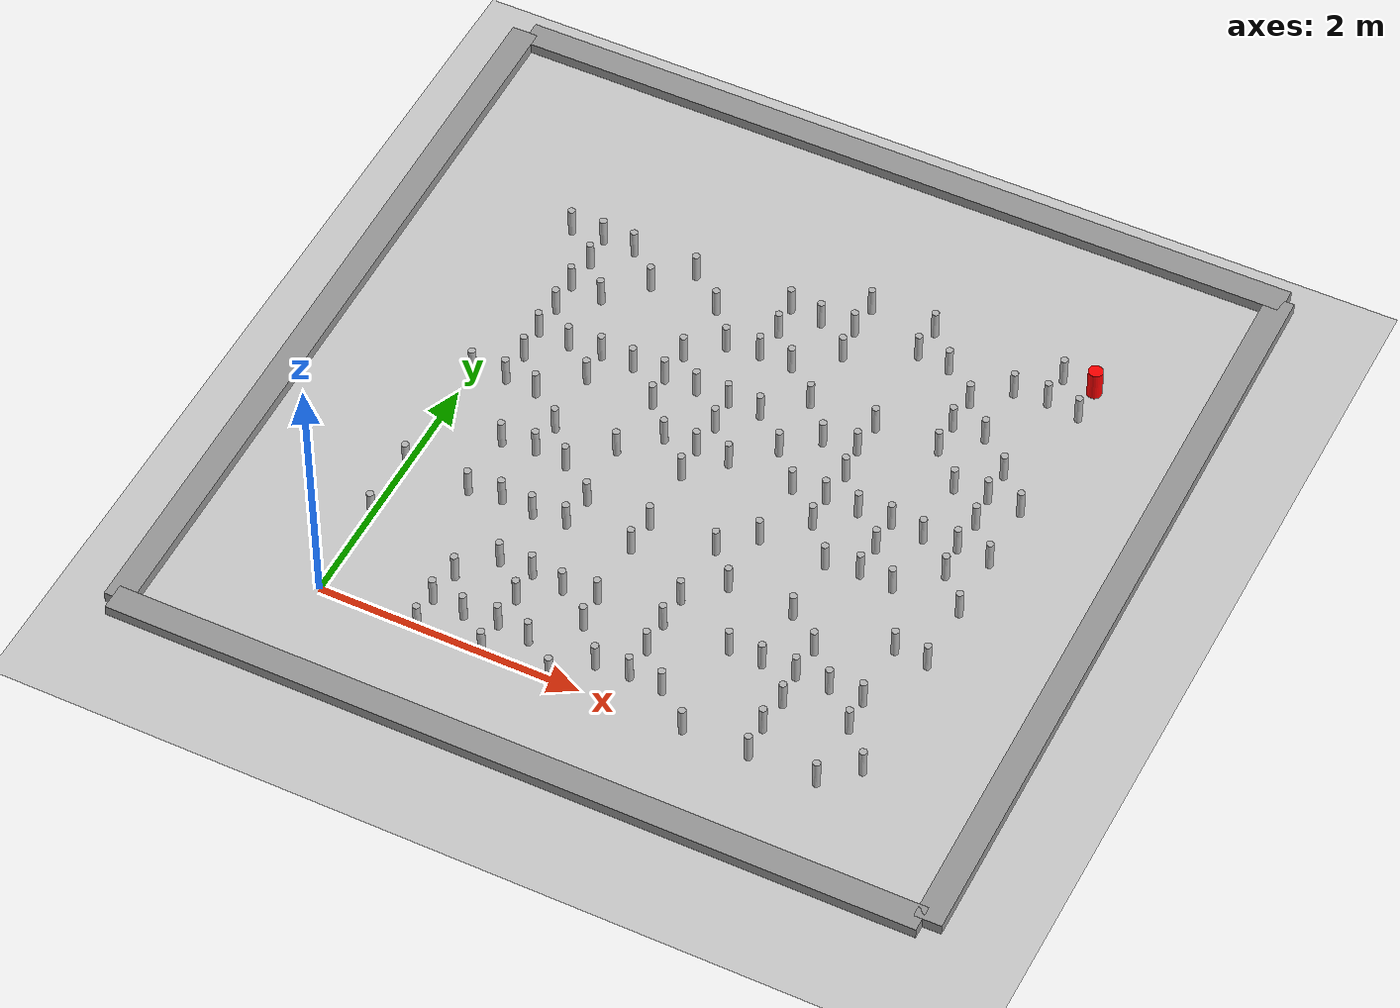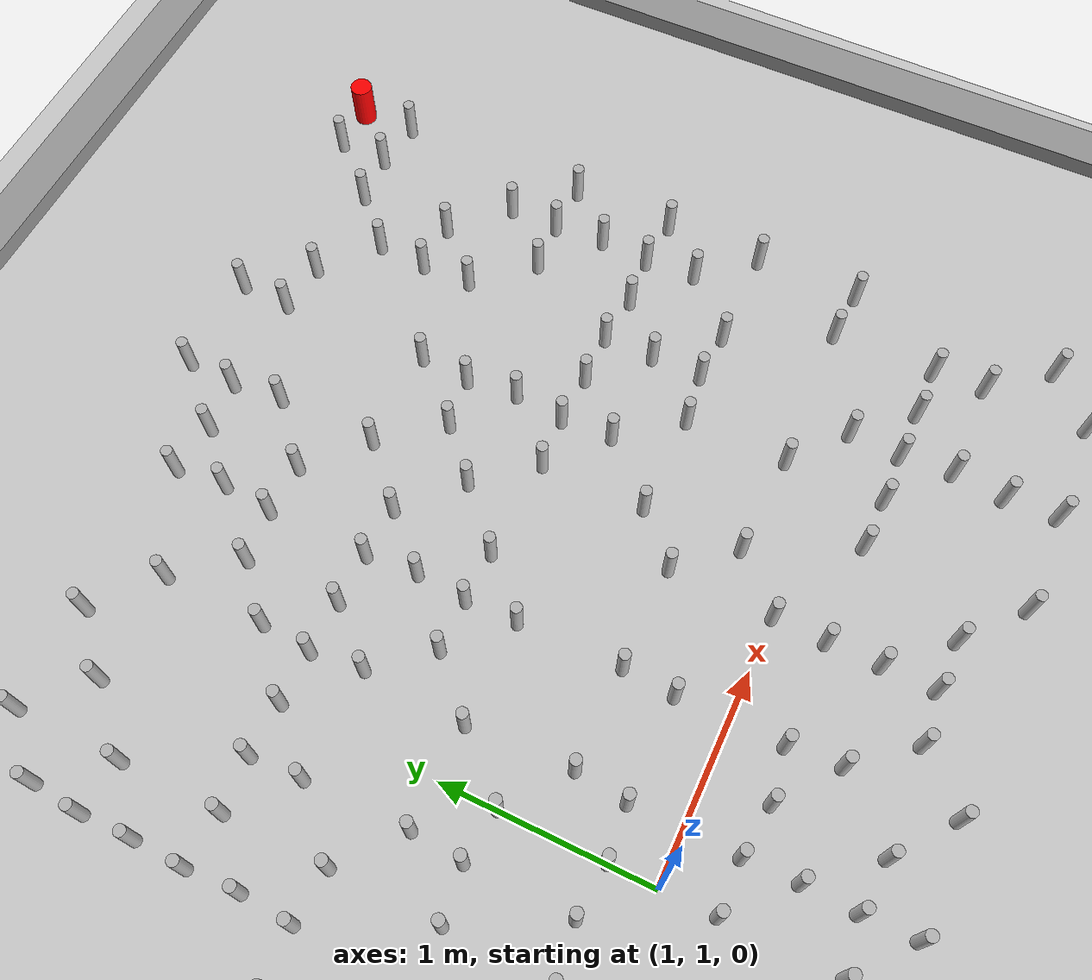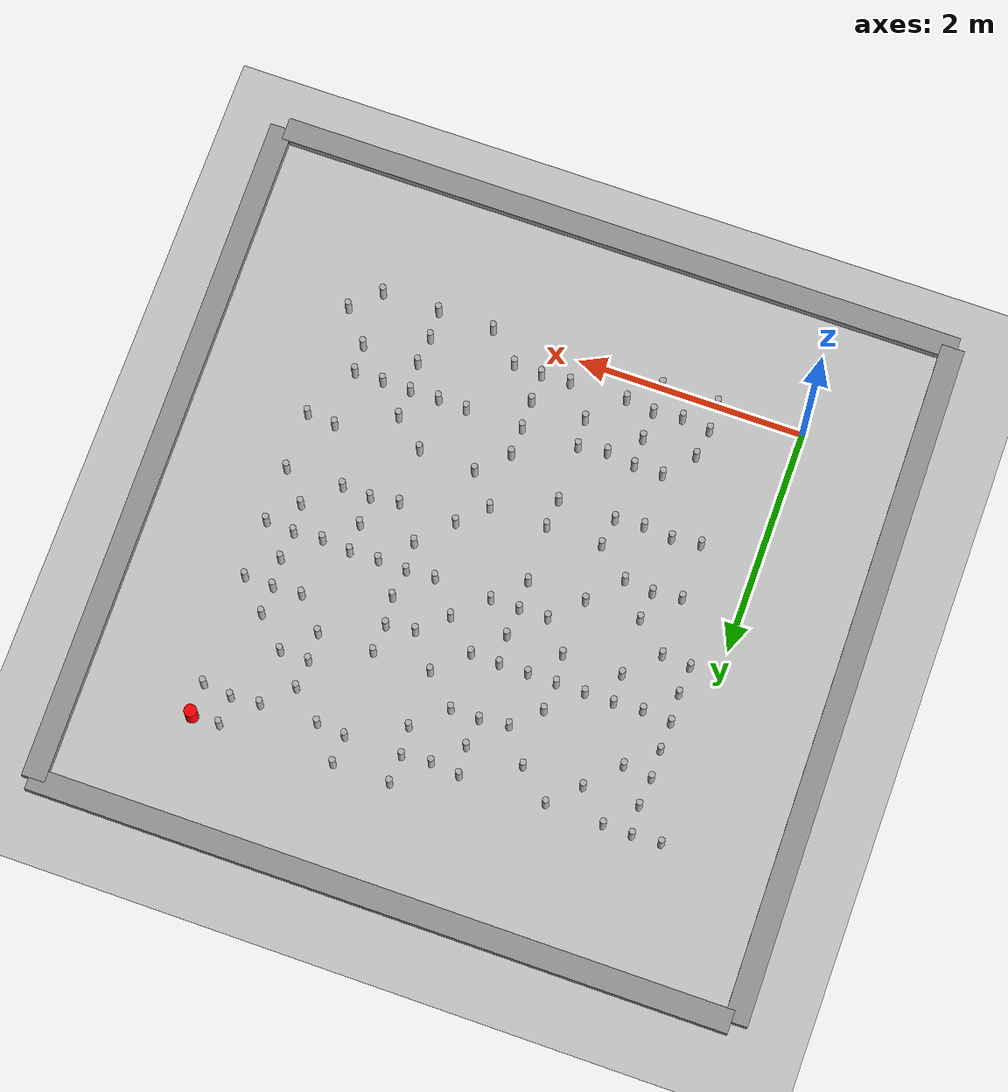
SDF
<sdf version="1.6">
 <world name="default">
  <light name="sun" type="directional">
   <pose>0 0 10 0 -0 0</pose>
   <diffuse>0.8 0.8 0.8 1</diffuse>
   <specular>0.1 0.1 0.1 1</specular>
   <attenuation>
    <range>1000</range>
    <constant>0.9</constant>
    <linear>0.01</linear>
    <quadratic>0.001</quadratic>
   </attenuation>
   <direction>-0.5 0.5 -1</direction>
  </light>
  <model name="ground_plane">
   <static>1</static>
   <link name="link">
    <collision name="collision">
     <geometry><plane><normal>0 0 1</normal><size>100 100</size></plane></geometry>
     <surface><friction><ode><mu>100</mu><mu2>50</mu2></ode></friction></surface>
    </collision>
    <visual name="visual">
     <cast_shadows>0</cast_shadows>
     <geometry><plane><normal>0 0 1</normal><size>100 100</size></plane></geometry>
     <material>
      <script><uri>file://media/materials/scripts/gazebo.material</uri><name>Gazebo/Grey</name></script>
     </material>
    </visual>
   </link>
  </model>
  <gravity>0 0 -9.8</gravity>
  <magnetic_field>6e-06 2.3e-05 -4.2e-05</magnetic_field>
  <atmosphere type="adiabatic"/>
  <physics name="default_physics" default="0" type="ode">
   <max_step_size>0.001</max_step_size>
   <real_time_factor>1</real_time_factor>
   <real_time_update_rate>1000</real_time_update_rate>
  </physics>
  <scene><ambient>0.4 0.4 0.4 1</ambient><background>0.7 0.7 0.7 1</background><shadows>1</shadows></scene>
  <spherical_coordinates>
   <surface_model>EARTH_WGS84</surface_model>
   <latitude_deg>0</latitude_deg>
   <longitude_deg>0</longitude_deg>
   <elevation>0</elevation>
   <heading_deg>0</heading_deg>
  </spherical_coordinates>
  <model name="goal">
   <link name="link">
    <pose>0 0 0.115 0 -0 0</pose>
    <inertial>
     <mass>0.0005</mass>
     <inertia><ixx>0.00058</ixx><ixy>0</ixy><ixz>0</ixz><iyy>0.00058</iyy><iyz>0</iyz><izz>0.00019</izz></inertia>
    </inertial>
    <visual name="visual">
     <geometry><cylinder><radius>0.055</radius><length>0.23</length></cylinder></geometry>
     <material>
      <script>
       <uri>model://beer/materials/scripts</uri>
       <uri>model://beer/materials/textures</uri>
       <name>Beer/Diffuse</name>
      </script>
      <ambient>1 0 0 1</ambient>
      <diffuse>1 0 0 1</diffuse>
      <specular>0 0 0 1</specular>
      <emissive>0 0 0 1</emissive>
      <shader type="vertex"><normal_map>__default__</normal_map></shader>
     </material>
    </visual>
    <collision name="collision">
     <geometry><cylinder><radius>0.055</radius><length>0.23</length></cylinder></geometry>
     <surface>
      <friction>
       <ode><mu>1</mu><mu2>1</mu2><fdir1>0 0 0</fdir1><slip1>0</slip1><slip2>0</slip2></ode>
       <torsional>
        <coefficient>1</coefficient>
        <patch_radius>0</patch_radius>
        <surface_radius>0</surface_radius>
        <use_patch_radius>1</use_patch_radius>
        <ode><slip>0</slip></ode>
       </torsional>
      </friction>
      <bounce><restitution_coefficient>0</restitution_coefficient><threshold>1e+06</threshold></bounce>
      <contact>
       <collide_without_contact>0</collide_without_contact>
       <collide_without_contact_bitmask>1</collide_without_contact_bitmask>
       <collide_bitmask>1</collide_bitmask>
       <ode>
        <soft_cfm>0</soft_cfm>
        <soft_erp>0.2</soft_erp>
        <kp>1e+13</kp>
        <kd>1</kd>
        <max_vel>0.01</max_vel>
        <min_depth>0</min_depth>
       </ode>
       <bullet>
        <split_impulse>1</split_impulse>
        <split_impulse_penetration_threshold>-0.01</split_impulse_penetration_threshold>
        <soft_cfm>0</soft_cfm>
        <soft_erp>0.2</soft_erp>
        <kp>1e+13</kp>
        <kd>1</kd>
       </bullet>
      </contact>
     </surface>
    </collision>
   </link>
   <static>0</static>
   <pose>4.0 4.0 -9e-06 -1e-06 -4e-06 0</pose>
  </model>
  <model name="wall1">
   <static>1</static>
   <link name="link">
    <pose>0 0 0.42 0 -0 0</pose>
    <collision name="collision"><geometry><box><size>6 0.2 0.084</size></box></geometry></collision>
    <visual name="visual">
     <cast_shadows>0</cast_shadows>
     <geometry><box><size>6 0.2 0.084</size></box></geometry>
     <material>
      <script>
       <uri>model://grey_wall/materials/scripts</uri>
       <uri>model://grey_wall/materials/textures</uri>
       <name>vrc/grey_wall</name>
      </script>
     </material>
    </visual>
   </link>
   <pose>-1 2.0 0 0 -0 -1.55905</pose>
  </model>
  <model name="wall2">
   <static>1</static>
   <link name="link">
    <pose>0 0 0.42 0 -0 0</pose>
    <collision name="collision"><geometry><box><size>6 0.2 0.084</size></box></geometry></collision>
    <visual name="visual">
     <cast_shadows>0</cast_shadows>
     <geometry><box><size>6 0.2 0.084</size></box></geometry>
     <material>
      <script>
       <uri>model://grey_wall/materials/scripts</uri>
       <uri>model://grey_wall/materials/textures</uri>
       <name>vrc/grey_wall</name>
      </script>
     </material>
    </visual>
   </link>
   <pose>2.0 5.0 0 0 -0 0</pose>
  </model>
  <model name="wall3">
   <static>1</static>
   <link name="link">
    <pose>0 0 0.42 0 -0 0</pose>
    <collision name="collision"><geometry><box><size>6 0.2 0.084</size></box></geometry></collision>
    <visual name="visual">
     <cast_shadows>0</cast_shadows>
     <geometry><box><size>6 0.2 0.084</size></box></geometry>
     <material>
      <script>
       <uri>model://grey_wall/materials/scripts</uri>
       <uri>model://grey_wall/materials/textures</uri>
       <name>vrc/grey_wall</name>
      </script>
     </material>
    </visual>
   </link>
   <pose>5.0 2.0 0 0 -0 -1.55905</pose>
  </model>
  <model name="wall4">
   <static>1</static>
   <link name="link">
    <pose>0 0 0.42 0 -0 0</pose>
    <collision name="collision"><geometry><box><size>6 0.2 0.084</size></box></geometry></collision>
    <visual name="visual">
     <cast_shadows>0</cast_shadows>
     <geometry><box><size>6 0.2 0.084</size></box></geometry>
     <material>
      <script>
       <uri>model://grey_wall/materials/scripts</uri>
       <uri>model://grey_wall/materials/textures</uri>
       <name>vrc/grey_wall</name>
      </script>
     </material>
    </visual>
   </link>
   <pose>2.0 -1 0 0 -0 0</pose>
  </model>
  <model name="can1">
   <link name="link">
    <pose>0 0 0.115 0 -0 0</pose>
    <inertial>
     <mass>0.39</mass>
     <inertia><ixx>0.00058</ixx><ixy>0</ixy><ixz>0</ixz><iyy>0.00058</iyy><iyz>0</iyz><izz>0.00019</izz></inertia>
    </inertial>
    <collision name="collision">
     <geometry><cylinder><radius>0.0275</radius><length>0.23</length></cylinder></geometry>
    </collision>
    <visual name="visual">
     <geometry><cylinder><radius>0.0275</radius><length>0.23</length></cylinder></geometry>
     <material>
      <script>
       <uri>model://beer/materials/scripts</uri>
       <uri>model://beer/materials/textures</uri>
       <name>Beer/Diffuse</name>
      </script>
     </material>
    </visual>
   </link>
   <pose>2.76914062124 2.0 -2e-06 1e-06 0 -9.5e-05</pose>
  </model>
  <model name="can2">
   <link name="link">
    <pose>0 0 0.115 0 -0 0</pose>
    <inertial>
     <mass>0.39</mass>
     <inertia><ixx>0.00058</ixx><ixy>0</ixy><ixz>0</ixz><iyy>0.00058</iyy><iyz>0</iyz><izz>0.00019</izz></inertia>
    </inertial>
    <collision name="collision">
     <geometry><cylinder><radius>0.0275</radius><length>0.23</length></cylinder></geometry>
    </collision>
    <visual name="visual">
     <geometry><cylinder><radius>0.0275</radius><length>0.23</length></cylinder></geometry>
     <material>
      <script>
       <uri>model://beer/materials/scripts</uri>
       <uri>model://beer/materials/textures</uri>
       <name>Beer/Diffuse</name>
      </script>
     </material>
    </visual>
   </link>
   <pose>1.25 2.75 -2e-06 1e-06 0 -9.5e-05</pose>
  </model>
  <model name="can3">
   <link name="link">
    <pose>0 0 0.115 0 -0 0</pose>
    <inertial>
     <mass>0.39</mass>
     <inertia><ixx>0.00058</ixx><ixy>0</ixy><ixz>0</ixz><iyy>0.00058</iyy><iyz>0</iyz><izz>0.00019</izz></inertia>
    </inertial>
    <collision name="collision">
     <geometry><cylinder><radius>0.0275</radius><length>0.23</length></cylinder></geometry>
    </collision>
    <visual name="visual">
     <geometry><cylinder><radius>0.0275</radius><length>0.23</length></cylinder></geometry>
     <material>
      <script>
       <uri>model://beer/materials/scripts</uri>
       <uri>model://beer/materials/textures</uri>
       <name>Beer/Diffuse</name>
      </script>
     </material>
    </visual>
   </link>
   <pose>3.26495329951 3.5 -2e-06 1e-06 0 -9.5e-05</pose>
  </model>
  <model name="can4">
   <link name="link">
    <pose>0 0 0.115 0 -0 0</pose>
    <inertial>
     <mass>0.39</mass>
     <inertia><ixx>0.00058</ixx><ixy>0</ixy><ixz>0</ixz><iyy>0.00058</iyy><iyz>0</iyz><izz>0.00019</izz></inertia>
    </inertial>
    <collision name="collision">
     <geometry><cylinder><radius>0.0275</radius><length>0.23</length></cylinder></geometry>
    </collision>
    <visual name="visual">
     <geometry><cylinder><radius>0.0275</radius><length>0.23</length></cylinder></geometry>
     <material>
      <script>
       <uri>model://beer/materials/scripts</uri>
       <uri>model://beer/materials/textures</uri>
       <name>Beer/Diffuse</name>
      </script>
     </material>
    </visual>
   </link>
   <pose>2.26718045114 3.0 -2e-06 1e-06 0 -9.5e-05</pose>
  </model>
  <model name="can5">
   <link name="link">
    <pose>0 0 0.115 0 -0 0</pose>
    <inertial>
     <mass>0.39</mass>
     <inertia><ixx>0.00058</ixx><ixy>0</ixy><ixz>0</ixz><iyy>0.00058</iyy><iyz>0</iyz><izz>0.00019</izz></inertia>
    </inertial>
    <collision name="collision">
     <geometry><cylinder><radius>0.0275</radius><length>0.23</length></cylinder></geometry>
    </collision>
    <visual name="visual">
     <geometry><cylinder><radius>0.0275</radius><length>0.23</length></cylinder></geometry>
     <material>
      <script>
       <uri>model://beer/materials/scripts</uri>
       <uri>model://beer/materials/textures</uri>
       <name>Beer/Diffuse</name>
      </script>
     </material>
    </visual>
   </link>
   <pose>2.5 2.23105684745 -2e-06 1e-06 0 -9.5e-05</pose>
  </model>
  <model name="can6">
   <link name="link">
    <pose>0 0 0.115 0 -0 0</pose>
    <inertial>
     <mass>0.39</mass>
     <inertia><ixx>0.00058</ixx><ixy>0</ixy><ixz>0</ixz><iyy>0.00058</iyy><iyz>0</iyz><izz>0.00019</izz></inertia>
    </inertial>
    <collision name="collision">
     <geometry><cylinder><radius>0.0275</radius><length>0.23</length></cylinder></geometry>
    </collision>
    <visual name="visual">
     <geometry><cylinder><radius>0.0275</radius><length>0.23</length></cylinder></geometry>
     <material>
      <script>
       <uri>model://beer/materials/scripts</uri>
       <uri>model://beer/materials/textures</uri>
       <name>Beer/Diffuse</name>
      </script>
     </material>
    </visual>
   </link>
   <pose>0.25 3.25 -2e-06 1e-06 0 -9.5e-05</pose>
  </model>
  <model name="can7">
   <link name="link">
    <pose>0 0 0.115 0 -0 0</pose>
    <inertial>
     <mass>0.39</mass>
     <inertia><ixx>0.00058</ixx><ixy>0</ixy><ixz>0</ixz><iyy>0.00058</iyy><iyz>0</iyz><izz>0.00019</izz></inertia>
    </inertial>
    <collision name="collision">
     <geometry><cylinder><radius>0.0275</radius><length>0.23</length></cylinder></geometry>
    </collision>
    <visual name="visual">
     <geometry><cylinder><radius>0.0275</radius><length>0.23</length></cylinder></geometry>
     <material>
      <script>
       <uri>model://beer/materials/scripts</uri>
       <uri>model://beer/materials/textures</uri>
       <name>Beer/Diffuse</name>
      </script>
     </material>
    </visual>
   </link>
   <pose>4.0 1.23062895829 -2e-06 1e-06 0 -9.5e-05</pose>
  </model>
  <model name="can8">
   <link name="link">
    <pose>0 0 0.115 0 -0 0</pose>
    <inertial>
     <mass>0.39</mass>
     <inertia><ixx>0.00058</ixx><ixy>0</ixy><ixz>0</ixz><iyy>0.00058</iyy><iyz>0</iyz><izz>0.00019</izz></inertia>
    </inertial>
    <collision name="collision">
     <geometry><cylinder><radius>0.0275</radius><length>0.23</length></cylinder></geometry>
    </collision>
    <visual name="visual">
     <geometry><cylinder><radius>0.0275</radius><length>0.23</length></cylinder></geometry>
     <material>
      <script>
       <uri>model://beer/materials/scripts</uri>
       <uri>model://beer/materials/textures</uri>
       <name>Beer/Diffuse</name>
      </script>
     </material>
    </visual>
   </link>
   <pose>2.26545907401 4.0 -2e-06 1e-06 0 -9.5e-05</pose>
  </model>
  <model name="can9">
   <link name="link">
    <pose>0 0 0.115 0 -0 0</pose>
    <inertial>
     <mass>0.39</mass>
     <inertia><ixx>0.00058</ixx><ixy>0</ixy><ixz>0</ixz><iyy>0.00058</iyy><iyz>0</iyz><izz>0.00019</izz></inertia>
    </inertial>
    <collision name="collision">
     <geometry><cylinder><radius>0.0275</radius><length>0.23</length></cylinder></geometry>
    </collision>
    <visual name="visual">
     <geometry><cylinder><radius>0.0275</radius><length>0.23</length></cylinder></geometry>
     <material>
      <script>
       <uri>model://beer/materials/scripts</uri>
       <uri>model://beer/materials/textures</uri>
       <name>Beer/Diffuse</name>
      </script>
     </material>
    </visual>
   </link>
   <pose>2.75 2.25 -2e-06 1e-06 0 -9.5e-05</pose>
  </model>
  <model name="can10">
   <link name="link">
    <pose>0 0 0.115 0 -0 0</pose>
    <inertial>
     <mass>0.39</mass>
     <inertia><ixx>0.00058</ixx><ixy>0</ixy><ixz>0</ixz><iyy>0.00058</iyy><iyz>0</iyz><izz>0.00019</izz></inertia>
    </inertial>
    <collision name="collision">
     <geometry><cylinder><radius>0.0275</radius><length>0.23</length></cylinder></geometry>
    </collision>
    <visual name="visual">
     <geometry><cylinder><radius>0.0275</radius><length>0.23</length></cylinder></geometry>
     <material>
      <script>
       <uri>model://beer/materials/scripts</uri>
       <uri>model://beer/materials/textures</uri>
       <name>Beer/Diffuse</name>
      </script>
     </material>
    </visual>
   </link>
   <pose>2.0 2.74515271717 -2e-06 1e-06 0 -9.5e-05</pose>
  </model>
  <model name="can11">
   <link name="link">
    <pose>0 0 0.115 0 -0 0</pose>
    <inertial>
     <mass>0.39</mass>
     <inertia><ixx>0.00058</ixx><ixy>0</ixy><ixz>0</ixz><iyy>0.00058</iyy><iyz>0</iyz><izz>0.00019</izz></inertia>
    </inertial>
    <collision name="collision">
     <geometry><cylinder><radius>0.0275</radius><length>0.23</length></cylinder></geometry>
    </collision>
    <visual name="visual">
     <geometry><cylinder><radius>0.0275</radius><length>0.23</length></cylinder></geometry>
     <material>
      <script>
       <uri>model://beer/materials/scripts</uri>
       <uri>model://beer/materials/textures</uri>
       <name>Beer/Diffuse</name>
      </script>
     </material>
    </visual>
   </link>
   <pose>2.7728491236 0.0 -2e-06 1e-06 0 -9.5e-05</pose>
  </model>
  <model name="can12">
   <link name="link">
    <pose>0 0 0.115 0 -0 0</pose>
    <inertial>
     <mass>0.39</mass>
     <inertia><ixx>0.00058</ixx><ixy>0</ixy><ixz>0</ixz><iyy>0.00058</iyy><iyz>0</iyz><izz>0.00019</izz></inertia>
    </inertial>
    <collision name="collision">
     <geometry><cylinder><radius>0.0275</radius><length>0.23</length></cylinder></geometry>
    </collision>
    <visual name="visual">
     <geometry><cylinder><radius>0.0275</radius><length>0.23</length></cylinder></geometry>
     <material>
      <script>
       <uri>model://beer/materials/scripts</uri>
       <uri>model://beer/materials/textures</uri>
       <name>Beer/Diffuse</name>
      </script>
     </material>
    </visual>
   </link>
   <pose>0.5 1.71648537448 -2e-06 1e-06 0 -9.5e-05</pose>
  </model>
  <model name="can13">
   <link name="link">
    <pose>0 0 0.115 0 -0 0</pose>
    <inertial>
     <mass>0.39</mass>
     <inertia><ixx>0.00058</ixx><ixy>0</ixy><ixz>0</ixz><iyy>0.00058</iyy><iyz>0</iyz><izz>0.00019</izz></inertia>
    </inertial>
    <collision name="collision">
     <geometry><cylinder><radius>0.0275</radius><length>0.23</length></cylinder></geometry>
    </collision>
    <visual name="visual">
     <geometry><cylinder><radius>0.0275</radius><length>0.23</length></cylinder></geometry>
     <material>
      <script>
       <uri>model://beer/materials/scripts</uri>
       <uri>model://beer/materials/textures</uri>
       <name>Beer/Diffuse</name>
      </script>
     </material>
    </visual>
   </link>
   <pose>3.75884397193 4.0 -2e-06 1e-06 0 -9.5e-05</pose>
  </model>
  <model name="can14">
   <link name="link">
    <pose>0 0 0.115 0 -0 0</pose>
    <inertial>
     <mass>0.39</mass>
     <inertia><ixx>0.00058</ixx><ixy>0</ixy><ixz>0</ixz><iyy>0.00058</iyy><iyz>0</iyz><izz>0.00019</izz></inertia>
    </inertial>
    <collision name="collision">
     <geometry><cylinder><radius>0.0275</radius><length>0.23</length></cylinder></geometry>
    </collision>
    <visual name="visual">
     <geometry><cylinder><radius>0.0275</radius><length>0.23</length></cylinder></geometry>
     <material>
      <script>
       <uri>model://beer/materials/scripts</uri>
       <uri>model://beer/materials/textures</uri>
       <name>Beer/Diffuse</name>
      </script>
     </material>
    </visual>
   </link>
   <pose>0.5 2.22964634361 -2e-06 1e-06 0 -9.5e-05</pose>
  </model>
  <model name="can15">
   <link name="link">
    <pose>0 0 0.115 0 -0 0</pose>
    <inertial>
     <mass>0.39</mass>
     <inertia><ixx>0.00058</ixx><ixy>0</ixy><ixz>0</ixz><iyy>0.00058</iyy><iyz>0</iyz><izz>0.00019</izz></inertia>
    </inertial>
    <collision name="collision">
     <geometry><cylinder><radius>0.0275</radius><length>0.23</length></cylinder></geometry>
    </collision>
    <visual name="visual">
     <geometry><cylinder><radius>0.0275</radius><length>0.23</length></cylinder></geometry>
     <material>
      <script>
       <uri>model://beer/materials/scripts</uri>
       <uri>model://beer/materials/textures</uri>
       <name>Beer/Diffuse</name>
      </script>
     </material>
    </visual>
   </link>
   <pose>3.25 2.25 -2e-06 1e-06 0 -9.5e-05</pose>
  </model>
  <model name="can16">
   <link name="link">
    <pose>0 0 0.115 0 -0 0</pose>
    <inertial>
     <mass>0.39</mass>
     <inertia><ixx>0.00058</ixx><ixy>0</ixy><ixz>0</ixz><iyy>0.00058</iyy><iyz>0</iyz><izz>0.00019</izz></inertia>
    </inertial>
    <collision name="collision">
     <geometry><cylinder><radius>0.0275</radius><length>0.23</length></cylinder></geometry>
    </collision>
    <visual name="visual">
     <geometry><cylinder><radius>0.0275</radius><length>0.23</length></cylinder></geometry>
     <material>
      <script>
       <uri>model://beer/materials/scripts</uri>
       <uri>model://beer/materials/textures</uri>
       <name>Beer/Diffuse</name>
      </script>
     </material>
    </visual>
   </link>
   <pose>4.0 1.74220794956 -2e-06 1e-06 0 -9.5e-05</pose>
  </model>
  <model name="can17">
   <link name="link">
    <pose>0 0 0.115 0 -0 0</pose>
    <inertial>
     <mass>0.39</mass>
     <inertia><ixx>0.00058</ixx><ixy>0</ixy><ixz>0</ixz><iyy>0.00058</iyy><iyz>0</iyz><izz>0.00019</izz></inertia>
    </inertial>
    <collision name="collision">
     <geometry><cylinder><radius>0.0275</radius><length>0.23</length></cylinder></geometry>
    </collision>
    <visual name="visual">
     <geometry><cylinder><radius>0.0275</radius><length>0.23</length></cylinder></geometry>
     <material>
      <script>
       <uri>model://beer/materials/scripts</uri>
       <uri>model://beer/materials/textures</uri>
       <name>Beer/Diffuse</name>
      </script>
     </material>
    </visual>
   </link>
   <pose>0.758827067788 3.5 -2e-06 1e-06 0 -9.5e-05</pose>
  </model>
  <model name="can18">
   <link name="link">
    <pose>0 0 0.115 0 -0 0</pose>
    <inertial>
     <mass>0.39</mass>
     <inertia><ixx>0.00058</ixx><ixy>0</ixy><ixz>0</ixz><iyy>0.00058</iyy><iyz>0</iyz><izz>0.00019</izz></inertia>
    </inertial>
    <collision name="collision">
     <geometry><cylinder><radius>0.0275</radius><length>0.23</length></cylinder></geometry>
    </collision>
    <visual name="visual">
     <geometry><cylinder><radius>0.0275</radius><length>0.23</length></cylinder></geometry>
     <material>
      <script>
       <uri>model://beer/materials/scripts</uri>
       <uri>model://beer/materials/textures</uri>
       <name>Beer/Diffuse</name>
      </script>
     </material>
    </visual>
   </link>
   <pose>2.76154148792 4.0 -2e-06 1e-06 0 -9.5e-05</pose>
  </model>
  <model name="can19">
   <link name="link">
    <pose>0 0 0.115 0 -0 0</pose>
    <inertial>
     <mass>0.39</mass>
     <inertia><ixx>0.00058</ixx><ixy>0</ixy><ixz>0</ixz><iyy>0.00058</iyy><iyz>0</iyz><izz>0.00019</izz></inertia>
    </inertial>
    <collision name="collision">
     <geometry><cylinder><radius>0.0275</radius><length>0.23</length></cylinder></geometry>
    </collision>
    <visual name="visual">
     <geometry><cylinder><radius>0.0275</radius><length>0.23</length></cylinder></geometry>
     <material>
      <script>
       <uri>model://beer/materials/scripts</uri>
       <uri>model://beer/materials/textures</uri>
       <name>Beer/Diffuse</name>
      </script>
     </material>
    </visual>
   </link>
   <pose>1.25368614977 2.0 -2e-06 1e-06 0 -9.5e-05</pose>
  </model>
  <model name="can20">
   <link name="link">
    <pose>0 0 0.115 0 -0 0</pose>
    <inertial>
     <mass>0.39</mass>
     <inertia><ixx>0.00058</ixx><ixy>0</ixy><ixz>0</ixz><iyy>0.00058</iyy><iyz>0</iyz><izz>0.00019</izz></inertia>
    </inertial>
    <collision name="collision">
     <geometry><cylinder><radius>0.0275</radius><length>0.23</length></cylinder></geometry>
    </collision>
    <visual name="visual">
     <geometry><cylinder><radius>0.0275</radius><length>0.23</length></cylinder></geometry>
     <material>
      <script>
       <uri>model://beer/materials/scripts</uri>
       <uri>model://beer/materials/textures</uri>
       <name>Beer/Diffuse</name>
      </script>
     </material>
    </visual>
   </link>
   <pose>3.77761734473 2.0 -2e-06 1e-06 0 -9.5e-05</pose>
  </model>
  <model name="can21">
   <link name="link">
    <pose>0 0 0.115 0 -0 0</pose>
    <inertial>
     <mass>0.39</mass>
     <inertia><ixx>0.00058</ixx><ixy>0</ixy><ixz>0</ixz><iyy>0.00058</iyy><iyz>0</iyz><izz>0.00019</izz></inertia>
    </inertial>
    <collision name="collision">
     <geometry><cylinder><radius>0.0275</radius><length>0.23</length></cylinder></geometry>
    </collision>
    <visual name="visual">
     <geometry><cylinder><radius>0.0275</radius><length>0.23</length></cylinder></geometry>
     <material>
      <script>
       <uri>model://beer/materials/scripts</uri>
       <uri>model://beer/materials/textures</uri>
       <name>Beer/Diffuse</name>
      </script>
     </material>
    </visual>
   </link>
   <pose>1.28084954127 2.5 -2e-06 1e-06 0 -9.5e-05</pose>
  </model>
  <model name="can22">
   <link name="link">
    <pose>0 0 0.115 0 -0 0</pose>
    <inertial>
     <mass>0.39</mass>
     <inertia><ixx>0.00058</ixx><ixy>0</ixy><ixz>0</ixz><iyy>0.00058</iyy><iyz>0</iyz><izz>0.00019</izz></inertia>
    </inertial>
    <collision name="collision">
     <geometry><cylinder><radius>0.0275</radius><length>0.23</length></cylinder></geometry>
    </collision>
    <visual name="visual">
     <geometry><cylinder><radius>0.0275</radius><length>0.23</length></cylinder></geometry>
     <material>
      <script>
       <uri>model://beer/materials/scripts</uri>
       <uri>model://beer/materials/textures</uri>
       <name>Beer/Diffuse</name>
      </script>
     </material>
    </visual>
   </link>
   <pose>3.77302308352 2.5 -2e-06 1e-06 0 -9.5e-05</pose>
  </model>
  <model name="can23">
   <link name="link">
    <pose>0 0 0.115 0 -0 0</pose>
    <inertial>
     <mass>0.39</mass>
     <inertia><ixx>0.00058</ixx><ixy>0</ixy><ixz>0</ixz><iyy>0.00058</iyy><iyz>0</iyz><izz>0.00019</izz></inertia>
    </inertial>
    <collision name="collision">
     <geometry><cylinder><radius>0.0275</radius><length>0.23</length></cylinder></geometry>
    </collision>
    <visual name="visual">
     <geometry><cylinder><radius>0.0275</radius><length>0.23</length></cylinder></geometry>
     <material>
      <script>
       <uri>model://beer/materials/scripts</uri>
       <uri>model://beer/materials/textures</uri>
       <name>Beer/Diffuse</name>
      </script>
     </material>
    </visual>
   </link>
   <pose>3.0 2.24248095322 -2e-06 1e-06 0 -9.5e-05</pose>
  </model>
  <model name="can24">
   <link name="link">
    <pose>0 0 0.115 0 -0 0</pose>
    <inertial>
     <mass>0.39</mass>
     <inertia><ixx>0.00058</ixx><ixy>0</ixy><ixz>0</ixz><iyy>0.00058</iyy><iyz>0</iyz><izz>0.00019</izz></inertia>
    </inertial>
    <collision name="collision">
     <geometry><cylinder><radius>0.0275</radius><length>0.23</length></cylinder></geometry>
    </collision>
    <visual name="visual">
     <geometry><cylinder><radius>0.0275</radius><length>0.23</length></cylinder></geometry>
     <material>
      <script>
       <uri>model://beer/materials/scripts</uri>
       <uri>model://beer/materials/textures</uri>
       <name>Beer/Diffuse</name>
      </script>
     </material>
    </visual>
   </link>
   <pose>0.771695028293 2.0 -2e-06 1e-06 0 -9.5e-05</pose>
  </model>
  <model name="can25">
   <link name="link">
    <pose>0 0 0.115 0 -0 0</pose>
    <inertial>
     <mass>0.39</mass>
     <inertia><ixx>0.00058</ixx><ixy>0</ixy><ixz>0</ixz><iyy>0.00058</iyy><iyz>0</iyz><izz>0.00019</izz></inertia>
    </inertial>
    <collision name="collision">
     <geometry><cylinder><radius>0.0275</radius><length>0.23</length></cylinder></geometry>
    </collision>
    <visual name="visual">
     <geometry><cylinder><radius>0.0275</radius><length>0.23</length></cylinder></geometry>
     <material>
      <script>
       <uri>model://beer/materials/scripts</uri>
       <uri>model://beer/materials/textures</uri>
       <name>Beer/Diffuse</name>
      </script>
     </material>
    </visual>
   </link>
   <pose>0.0 3.73681978817 -2e-06 1e-06 0 -9.5e-05</pose>
  </model>
  <model name="can26">
   <link name="link">
    <pose>0 0 0.115 0 -0 0</pose>
    <inertial>
     <mass>0.39</mass>
     <inertia><ixx>0.00058</ixx><ixy>0</ixy><ixz>0</ixz><iyy>0.00058</iyy><iyz>0</iyz><izz>0.00019</izz></inertia>
    </inertial>
    <collision name="collision">
     <geometry><cylinder><radius>0.0275</radius><length>0.23</length></cylinder></geometry>
    </collision>
    <visual name="visual">
     <geometry><cylinder><radius>0.0275</radius><length>0.23</length></cylinder></geometry>
     <material>
      <script>
       <uri>model://beer/materials/scripts</uri>
       <uri>model://beer/materials/textures</uri>
       <name>Beer/Diffuse</name>
      </script>
     </material>
    </visual>
   </link>
   <pose>2.25908990194 1.0 -2e-06 1e-06 0 -9.5e-05</pose>
  </model>
  <model name="can27">
   <link name="link">
    <pose>0 0 0.115 0 -0 0</pose>
    <inertial>
     <mass>0.39</mass>
     <inertia><ixx>0.00058</ixx><ixy>0</ixy><ixz>0</ixz><iyy>0.00058</iyy><iyz>0</iyz><izz>0.00019</izz></inertia>
    </inertial>
    <collision name="collision">
     <geometry><cylinder><radius>0.0275</radius><length>0.23</length></cylinder></geometry>
    </collision>
    <visual name="visual">
     <geometry><cylinder><radius>0.0275</radius><length>0.23</length></cylinder></geometry>
     <material>
      <script>
       <uri>model://beer/materials/scripts</uri>
       <uri>model://beer/materials/textures</uri>
       <name>Beer/Diffuse</name>
      </script>
     </material>
    </visual>
   </link>
   <pose>2.27713867576 3.5 -2e-06 1e-06 0 -9.5e-05</pose>
  </model>
  <model name="can28">
   <link name="link">
    <pose>0 0 0.115 0 -0 0</pose>
    <inertial>
     <mass>0.39</mass>
     <inertia><ixx>0.00058</ixx><ixy>0</ixy><ixz>0</ixz><iyy>0.00058</iyy><iyz>0</iyz><izz>0.00019</izz></inertia>
    </inertial>
    <collision name="collision">
     <geometry><cylinder><radius>0.0275</radius><length>0.23</length></cylinder></geometry>
    </collision>
    <visual name="visual">
     <geometry><cylinder><radius>0.0275</radius><length>0.23</length></cylinder></geometry>
     <material>
      <script>
       <uri>model://beer/materials/scripts</uri>
       <uri>model://beer/materials/textures</uri>
       <name>Beer/Diffuse</name>
      </script>
     </material>
    </visual>
   </link>
   <pose>0.0 0.73987362745 -2e-06 1e-06 0 -9.5e-05</pose>
  </model>
  <model name="can29">
   <link name="link">
    <pose>0 0 0.115 0 -0 0</pose>
    <inertial>
     <mass>0.39</mass>
     <inertia><ixx>0.00058</ixx><ixy>0</ixy><ixz>0</ixz><iyy>0.00058</iyy><iyz>0</iyz><izz>0.00019</izz></inertia>
    </inertial>
    <collision name="collision">
     <geometry><cylinder><radius>0.0275</radius><length>0.23</length></cylinder></geometry>
    </collision>
    <visual name="visual">
     <geometry><cylinder><radius>0.0275</radius><length>0.23</length></cylinder></geometry>
     <material>
      <script>
       <uri>model://beer/materials/scripts</uri>
       <uri>model://beer/materials/textures</uri>
       <name>Beer/Diffuse</name>
      </script>
     </material>
    </visual>
   </link>
   <pose>3.5 2.73313233826 -2e-06 1e-06 0 -9.5e-05</pose>
  </model>
  <model name="can30">
   <link name="link">
    <pose>0 0 0.115 0 -0 0</pose>
    <inertial>
     <mass>0.39</mass>
     <inertia><ixx>0.00058</ixx><ixy>0</ixy><ixz>0</ixz><iyy>0.00058</iyy><iyz>0</iyz><izz>0.00019</izz></inertia>
    </inertial>
    <collision name="collision">
     <geometry><cylinder><radius>0.0275</radius><length>0.23</length></cylinder></geometry>
    </collision>
    <visual name="visual">
     <geometry><cylinder><radius>0.0275</radius><length>0.23</length></cylinder></geometry>
     <material>
      <script>
       <uri>model://beer/materials/scripts</uri>
       <uri>model://beer/materials/textures</uri>
       <name>Beer/Diffuse</name>
      </script>
     </material>
    </visual>
   </link>
   <pose>2.26679566876 2.5 -2e-06 1e-06 0 -9.5e-05</pose>
  </model>
  <model name="can31">
   <link name="link">
    <pose>0 0 0.115 0 -0 0</pose>
    <inertial>
     <mass>0.39</mass>
     <inertia><ixx>0.00058</ixx><ixy>0</ixy><ixz>0</ixz><iyy>0.00058</iyy><iyz>0</iyz><izz>0.00019</izz></inertia>
    </inertial>
    <collision name="collision">
     <geometry><cylinder><radius>0.0275</radius><length>0.23</length></cylinder></geometry>
    </collision>
    <visual name="visual">
     <geometry><cylinder><radius>0.0275</radius><length>0.23</length></cylinder></geometry>
     <material>
      <script>
       <uri>model://beer/materials/scripts</uri>
       <uri>model://beer/materials/textures</uri>
       <name>Beer/Diffuse</name>
      </script>
     </material>
    </visual>
   </link>
   <pose>3.75 1.25 -2e-06 1e-06 0 -9.5e-05</pose>
  </model>
  <model name="can32">
   <link name="link">
    <pose>0 0 0.115 0 -0 0</pose>
    <inertial>
     <mass>0.39</mass>
     <inertia><ixx>0.00058</ixx><ixy>0</ixy><ixz>0</ixz><iyy>0.00058</iyy><iyz>0</iyz><izz>0.00019</izz></inertia>
    </inertial>
    <collision name="collision">
     <geometry><cylinder><radius>0.0275</radius><length>0.23</length></cylinder></geometry>
    </collision>
    <visual name="visual">
     <geometry><cylinder><radius>0.0275</radius><length>0.23</length></cylinder></geometry>
     <material>
      <script>
       <uri>model://beer/materials/scripts</uri>
       <uri>model://beer/materials/textures</uri>
       <name>Beer/Diffuse</name>
      </script>
     </material>
    </visual>
   </link>
   <pose>1.75 2.25 -2e-06 1e-06 0 -9.5e-05</pose>
  </model>
  <model name="can33">
   <link name="link">
    <pose>0 0 0.115 0 -0 0</pose>
    <inertial>
     <mass>0.39</mass>
     <inertia><ixx>0.00058</ixx><ixy>0</ixy><ixz>0</ixz><iyy>0.00058</iyy><iyz>0</iyz><izz>0.00019</izz></inertia>
    </inertial>
    <collision name="collision">
     <geometry><cylinder><radius>0.0275</radius><length>0.23</length></cylinder></geometry>
    </collision>
    <visual name="visual">
     <geometry><cylinder><radius>0.0275</radius><length>0.23</length></cylinder></geometry>
     <material>
      <script>
       <uri>model://beer/materials/scripts</uri>
       <uri>model://beer/materials/textures</uri>
       <name>Beer/Diffuse</name>
      </script>
     </material>
    </visual>
   </link>
   <pose>1.25 1.25 -2e-06 1e-06 0 -9.5e-05</pose>
  </model>
  <model name="can34">
   <link name="link">
    <pose>0 0 0.115 0 -0 0</pose>
    <inertial>
     <mass>0.39</mass>
     <inertia><ixx>0.00058</ixx><ixy>0</ixy><ixz>0</ixz><iyy>0.00058</iyy><iyz>0</iyz><izz>0.00019</izz></inertia>
    </inertial>
    <collision name="collision">
     <geometry><cylinder><radius>0.0275</radius><length>0.23</length></cylinder></geometry>
    </collision>
    <visual name="visual">
     <geometry><cylinder><radius>0.0275</radius><length>0.23</length></cylinder></geometry>
     <material>
      <script>
       <uri>model://beer/materials/scripts</uri>
       <uri>model://beer/materials/textures</uri>
       <name>Beer/Diffuse</name>
      </script>
     </material>
    </visual>
   </link>
   <pose>2.75 3.75 -2e-06 1e-06 0 -9.5e-05</pose>
  </model>
  <model name="can35">
   <link name="link">
    <pose>0 0 0.115 0 -0 0</pose>
    <inertial>
     <mass>0.39</mass>
     <inertia><ixx>0.00058</ixx><ixy>0</ixy><ixz>0</ixz><iyy>0.00058</iyy><iyz>0</iyz><izz>0.00019</izz></inertia>
    </inertial>
    <collision name="collision">
     <geometry><cylinder><radius>0.0275</radius><length>0.23</length></cylinder></geometry>
    </collision>
    <visual name="visual">
     <geometry><cylinder><radius>0.0275</radius><length>0.23</length></cylinder></geometry>
     <material>
      <script>
       <uri>model://beer/materials/scripts</uri>
       <uri>model://beer/materials/textures</uri>
       <name>Beer/Diffuse</name>
      </script>
     </material>
    </visual>
   </link>
   <pose>0.25 3.75 -2e-06 1e-06 0 -9.5e-05</pose>
  </model>
  <model name="can36">
   <link name="link">
    <pose>0 0 0.115 0 -0 0</pose>
    <inertial>
     <mass>0.39</mass>
     <inertia><ixx>0.00058</ixx><ixy>0</ixy><ixz>0</ixz><iyy>0.00058</iyy><iyz>0</iyz><izz>0.00019</izz></inertia>
    </inertial>
    <collision name="collision">
     <geometry><cylinder><radius>0.0275</radius><length>0.23</length></cylinder></geometry>
    </collision>
    <visual name="visual">
     <geometry><cylinder><radius>0.0275</radius><length>0.23</length></cylinder></geometry>
     <material>
      <script>
       <uri>model://beer/materials/scripts</uri>
       <uri>model://beer/materials/textures</uri>
       <name>Beer/Diffuse</name>
      </script>
     </material>
    </visual>
   </link>
   <pose>0.761350480602 2.5 -2e-06 1e-06 0 -9.5e-05</pose>
  </model>
  <model name="can37">
   <link name="link">
    <pose>0 0 0.115 0 -0 0</pose>
    <inertial>
     <mass>0.39</mass>
     <inertia><ixx>0.00058</ixx><ixy>0</ixy><ixz>0</ixz><iyy>0.00058</iyy><iyz>0</iyz><izz>0.00019</izz></inertia>
    </inertial>
    <collision name="collision">
     <geometry><cylinder><radius>0.0275</radius><length>0.23</length></cylinder></geometry>
    </collision>
    <visual name="visual">
     <geometry><cylinder><radius>0.0275</radius><length>0.23</length></cylinder></geometry>
     <material>
      <script>
       <uri>model://beer/materials/scripts</uri>
       <uri>model://beer/materials/textures</uri>
       <name>Beer/Diffuse</name>
      </script>
     </material>
    </visual>
   </link>
   <pose>1.75 3.75 -2e-06 1e-06 0 -9.5e-05</pose>
  </model>
  <model name="can38">
   <link name="link">
    <pose>0 0 0.115 0 -0 0</pose>
    <inertial>
     <mass>0.39</mass>
     <inertia><ixx>0.00058</ixx><ixy>0</ixy><ixz>0</ixz><iyy>0.00058</iyy><iyz>0</iyz><izz>0.00019</izz></inertia>
    </inertial>
    <collision name="collision">
     <geometry><cylinder><radius>0.0275</radius><length>0.23</length></cylinder></geometry>
    </collision>
    <visual name="visual">
     <geometry><cylinder><radius>0.0275</radius><length>0.23</length></cylinder></geometry>
     <material>
      <script>
       <uri>model://beer/materials/scripts</uri>
       <uri>model://beer/materials/textures</uri>
       <name>Beer/Diffuse</name>
      </script>
     </material>
    </visual>
   </link>
   <pose>0.5 1.21987626861 -2e-06 1e-06 0 -9.5e-05</pose>
  </model>
  <model name="can39">
   <link name="link">
    <pose>0 0 0.115 0 -0 0</pose>
    <inertial>
     <mass>0.39</mass>
     <inertia><ixx>0.00058</ixx><ixy>0</ixy><ixz>0</ixz><iyy>0.00058</iyy><iyz>0</iyz><izz>0.00019</izz></inertia>
    </inertial>
    <collision name="collision">
     <geometry><cylinder><radius>0.0275</radius><length>0.23</length></cylinder></geometry>
    </collision>
    <visual name="visual">
     <geometry><cylinder><radius>0.0275</radius><length>0.23</length></cylinder></geometry>
     <material>
      <script>
       <uri>model://beer/materials/scripts</uri>
       <uri>model://beer/materials/textures</uri>
       <name>Beer/Diffuse</name>
      </script>
     </material>
    </visual>
   </link>
   <pose>1.27181490617 3.0 -2e-06 1e-06 0 -9.5e-05</pose>
  </model>
  <model name="can40">
   <link name="link">
    <pose>0 0 0.115 0 -0 0</pose>
    <inertial>
     <mass>0.39</mass>
     <inertia><ixx>0.00058</ixx><ixy>0</ixy><ixz>0</ixz><iyy>0.00058</iyy><iyz>0</iyz><izz>0.00019</izz></inertia>
    </inertial>
    <collision name="collision">
     <geometry><cylinder><radius>0.0275</radius><length>0.23</length></cylinder></geometry>
    </collision>
    <visual name="visual">
     <geometry><cylinder><radius>0.0275</radius><length>0.23</length></cylinder></geometry>
     <material>
      <script>
       <uri>model://beer/materials/scripts</uri>
       <uri>model://beer/materials/textures</uri>
       <name>Beer/Diffuse</name>
      </script>
     </material>
    </visual>
   </link>
   <pose>0.784743643753 0.5 -2e-06 1e-06 0 -9.5e-05</pose>
  </model>
  <model name="can41">
   <link name="link">
    <pose>0 0 0.115 0 -0 0</pose>
    <inertial>
     <mass>0.39</mass>
     <inertia><ixx>0.00058</ixx><ixy>0</ixy><ixz>0</ixz><iyy>0.00058</iyy><iyz>0</iyz><izz>0.00019</izz></inertia>
    </inertial>
    <collision name="collision">
     <geometry><cylinder><radius>0.0275</radius><length>0.23</length></cylinder></geometry>
    </collision>
    <visual name="visual">
     <geometry><cylinder><radius>0.0275</radius><length>0.23</length></cylinder></geometry>
     <material>
      <script>
       <uri>model://beer/materials/scripts</uri>
       <uri>model://beer/materials/textures</uri>
       <name>Beer/Diffuse</name>
      </script>
     </material>
    </visual>
   </link>
   <pose>2.25 0.75 -2e-06 1e-06 0 -9.5e-05</pose>
  </model>
  <model name="can42">
   <link name="link">
    <pose>0 0 0.115 0 -0 0</pose>
    <inertial>
     <mass>0.39</mass>
     <inertia><ixx>0.00058</ixx><ixy>0</ixy><ixz>0</ixz><iyy>0.00058</iyy><iyz>0</iyz><izz>0.00019</izz></inertia>
    </inertial>
    <collision name="collision">
     <geometry><cylinder><radius>0.0275</radius><length>0.23</length></cylinder></geometry>
    </collision>
    <visual name="visual">
     <geometry><cylinder><radius>0.0275</radius><length>0.23</length></cylinder></geometry>
     <material>
      <script>
       <uri>model://beer/materials/scripts</uri>
       <uri>model://beer/materials/textures</uri>
       <name>Beer/Diffuse</name>
      </script>
     </material>
    </visual>
   </link>
   <pose>1.0 0.748625102724 -2e-06 1e-06 0 -9.5e-05</pose>
  </model>
  <model name="can43">
   <link name="link">
    <pose>0 0 0.115 0 -0 0</pose>
    <inertial>
     <mass>0.39</mass>
     <inertia><ixx>0.00058</ixx><ixy>0</ixy><ixz>0</ixz><iyy>0.00058</iyy><iyz>0</iyz><izz>0.00019</izz></inertia>
    </inertial>
    <collision name="collision">
     <geometry><cylinder><radius>0.0275</radius><length>0.23</length></cylinder></geometry>
    </collision>
    <visual name="visual">
     <geometry><cylinder><radius>0.0275</radius><length>0.23</length></cylinder></geometry>
     <material>
      <script>
       <uri>model://beer/materials/scripts</uri>
       <uri>model://beer/materials/textures</uri>
       <name>Beer/Diffuse</name>
      </script>
     </material>
    </visual>
   </link>
   <pose>1.25782060675 0.5 -2e-06 1e-06 0 -9.5e-05</pose>
  </model>
  <model name="can44">
   <link name="link">
    <pose>0 0 0.115 0 -0 0</pose>
    <inertial>
     <mass>0.39</mass>
     <inertia><ixx>0.00058</ixx><ixy>0</ixy><ixz>0</ixz><iyy>0.00058</iyy><iyz>0</iyz><izz>0.00019</izz></inertia>
    </inertial>
    <collision name="collision">
     <geometry><cylinder><radius>0.0275</radius><length>0.23</length></cylinder></geometry>
    </collision>
    <visual name="visual">
     <geometry><cylinder><radius>0.0275</radius><length>0.23</length></cylinder></geometry>
     <material>
      <script>
       <uri>model://beer/materials/scripts</uri>
       <uri>model://beer/materials/textures</uri>
       <name>Beer/Diffuse</name>
      </script>
     </material>
    </visual>
   </link>
   <pose>1.77244590395 0.5 -2e-06 1e-06 0 -9.5e-05</pose>
  </model>
  <model name="can45">
   <link name="link">
    <pose>0 0 0.115 0 -0 0</pose>
    <inertial>
     <mass>0.39</mass>
     <inertia><ixx>0.00058</ixx><ixy>0</ixy><ixz>0</ixz><iyy>0.00058</iyy><iyz>0</iyz><izz>0.00019</izz></inertia>
    </inertial>
    <collision name="collision">
     <geometry><cylinder><radius>0.0275</radius><length>0.23</length></cylinder></geometry>
    </collision>
    <visual name="visual">
     <geometry><cylinder><radius>0.0275</radius><length>0.23</length></cylinder></geometry>
     <material>
      <script>
       <uri>model://beer/materials/scripts</uri>
       <uri>model://beer/materials/textures</uri>
       <name>Beer/Diffuse</name>
      </script>
     </material>
    </visual>
   </link>
   <pose>1.0 1.72092333949 -2e-06 1e-06 0 -9.5e-05</pose>
  </model>
  <model name="can46">
   <link name="link">
    <pose>0 0 0.115 0 -0 0</pose>
    <inertial>
     <mass>0.39</mass>
     <inertia><ixx>0.00058</ixx><ixy>0</ixy><ixz>0</ixz><iyy>0.00058</iyy><iyz>0</iyz><izz>0.00019</izz></inertia>
    </inertial>
    <collision name="collision">
     <geometry><cylinder><radius>0.0275</radius><length>0.23</length></cylinder></geometry>
    </collision>
    <visual name="visual">
     <geometry><cylinder><radius>0.0275</radius><length>0.23</length></cylinder></geometry>
     <material>
      <script>
       <uri>model://beer/materials/scripts</uri>
       <uri>model://beer/materials/textures</uri>
       <name>Beer/Diffuse</name>
      </script>
     </material>
    </visual>
   </link>
   <pose>4.0 2.74399311653 -2e-06 1e-06 0 -9.5e-05</pose>
  </model>
  <model name="can47">
   <link name="link">
    <pose>0 0 0.115 0 -0 0</pose>
    <inertial>
     <mass>0.39</mass>
     <inertia><ixx>0.00058</ixx><ixy>0</ixy><ixz>0</ixz><iyy>0.00058</iyy><iyz>0</iyz><izz>0.00019</izz></inertia>
    </inertial>
    <collision name="collision">
     <geometry><cylinder><radius>0.0275</radius><length>0.23</length></cylinder></geometry>
    </collision>
    <visual name="visual">
     <geometry><cylinder><radius>0.0275</radius><length>0.23</length></cylinder></geometry>
     <material>
      <script>
       <uri>model://beer/materials/scripts</uri>
       <uri>model://beer/materials/textures</uri>
       <name>Beer/Diffuse</name>
      </script>
     </material>
    </visual>
   </link>
   <pose>3.76723646011 0.0 -2e-06 1e-06 0 -9.5e-05</pose>
  </model>
  <model name="can48">
   <link name="link">
    <pose>0 0 0.115 0 -0 0</pose>
    <inertial>
     <mass>0.39</mass>
     <inertia><ixx>0.00058</ixx><ixy>0</ixy><ixz>0</ixz><iyy>0.00058</iyy><iyz>0</iyz><izz>0.00019</izz></inertia>
    </inertial>
    <collision name="collision">
     <geometry><cylinder><radius>0.0275</radius><length>0.23</length></cylinder></geometry>
    </collision>
    <visual name="visual">
     <geometry><cylinder><radius>0.0275</radius><length>0.23</length></cylinder></geometry>
     <material>
      <script>
       <uri>model://beer/materials/scripts</uri>
       <uri>model://beer/materials/textures</uri>
       <name>Beer/Diffuse</name>
      </script>
     </material>
    </visual>
   </link>
   <pose>2.0 3.72316663458 -2e-06 1e-06 0 -9.5e-05</pose>
  </model>
  <model name="can49">
   <link name="link">
    <pose>0 0 0.115 0 -0 0</pose>
    <inertial>
     <mass>0.39</mass>
     <inertia><ixx>0.00058</ixx><ixy>0</ixy><ixz>0</ixz><iyy>0.00058</iyy><iyz>0</iyz><izz>0.00019</izz></inertia>
    </inertial>
    <collision name="collision">
     <geometry><cylinder><radius>0.0275</radius><length>0.23</length></cylinder></geometry>
    </collision>
    <visual name="visual">
     <geometry><cylinder><radius>0.0275</radius><length>0.23</length></cylinder></geometry>
     <material>
      <script>
       <uri>model://beer/materials/scripts</uri>
       <uri>model://beer/materials/textures</uri>
       <name>Beer/Diffuse</name>
      </script>
     </material>
    </visual>
   </link>
   <pose>1.5 0.715805118168 -2e-06 1e-06 0 -9.5e-05</pose>
  </model>
  <model name="can50">
   <link name="link">
    <pose>0 0 0.115 0 -0 0</pose>
    <inertial>
     <mass>0.39</mass>
     <inertia><ixx>0.00058</ixx><ixy>0</ixy><ixz>0</ixz><iyy>0.00058</iyy><iyz>0</iyz><izz>0.00019</izz></inertia>
    </inertial>
    <collision name="collision">
     <geometry><cylinder><radius>0.0275</radius><length>0.23</length></cylinder></geometry>
    </collision>
    <visual name="visual">
     <geometry><cylinder><radius>0.0275</radius><length>0.23</length></cylinder></geometry>
     <material>
      <script>
       <uri>model://beer/materials/scripts</uri>
       <uri>model://beer/materials/textures</uri>
       <name>Beer/Diffuse</name>
      </script>
     </material>
    </visual>
   </link>
   <pose>0.75 0.25 -2e-06 1e-06 0 -9.5e-05</pose>
  </model>
  <model name="can51">
   <link name="link">
    <pose>0 0 0.115 0 -0 0</pose>
    <inertial>
     <mass>0.39</mass>
     <inertia><ixx>0.00058</ixx><ixy>0</ixy><ixz>0</ixz><iyy>0.00058</iyy><iyz>0</iyz><izz>0.00019</izz></inertia>
    </inertial>
    <collision name="collision">
     <geometry><cylinder><radius>0.0275</radius><length>0.23</length></cylinder></geometry>
    </collision>
    <visual name="visual">
     <geometry><cylinder><radius>0.0275</radius><length>0.23</length></cylinder></geometry>
     <material>
      <script>
       <uri>model://beer/materials/scripts</uri>
       <uri>model://beer/materials/textures</uri>
       <name>Beer/Diffuse</name>
      </script>
     </material>
    </visual>
   </link>
   <pose>1.75 2.75 -2e-06 1e-06 0 -9.5e-05</pose>
  </model>
  <model name="can52">
   <link name="link">
    <pose>0 0 0.115 0 -0 0</pose>
    <inertial>
     <mass>0.39</mass>
     <inertia><ixx>0.00058</ixx><ixy>0</ixy><ixz>0</ixz><iyy>0.00058</iyy><iyz>0</iyz><izz>0.00019</izz></inertia>
    </inertial>
    <collision name="collision">
     <geometry><cylinder><radius>0.0275</radius><length>0.23</length></cylinder></geometry>
    </collision>
    <visual name="visual">
     <geometry><cylinder><radius>0.0275</radius><length>0.23</length></cylinder></geometry>
     <material>
      <script>
       <uri>model://beer/materials/scripts</uri>
       <uri>model://beer/materials/textures</uri>
       <name>Beer/Diffuse</name>
      </script>
     </material>
    </visual>
   </link>
   <pose>1.0 0.218534555931 -2e-06 1e-06 0 -9.5e-05</pose>
  </model>
  <model name="can53">
   <link name="link">
    <pose>0 0 0.115 0 -0 0</pose>
    <inertial>
     <mass>0.39</mass>
     <inertia><ixx>0.00058</ixx><ixy>0</ixy><ixz>0</ixz><iyy>0.00058</iyy><iyz>0</iyz><izz>0.00019</izz></inertia>
    </inertial>
    <collision name="collision">
     <geometry><cylinder><radius>0.0275</radius><length>0.23</length></cylinder></geometry>
    </collision>
    <visual name="visual">
     <geometry><cylinder><radius>0.0275</radius><length>0.23</length></cylinder></geometry>
     <material>
      <script>
       <uri>model://beer/materials/scripts</uri>
       <uri>model://beer/materials/textures</uri>
       <name>Beer/Diffuse</name>
      </script>
     </material>
    </visual>
   </link>
   <pose>2.75 2.75 -2e-06 1e-06 0 -9.5e-05</pose>
  </model>
  <model name="can54">
   <link name="link">
    <pose>0 0 0.115 0 -0 0</pose>
    <inertial>
     <mass>0.39</mass>
     <inertia><ixx>0.00058</ixx><ixy>0</ixy><ixz>0</ixz><iyy>0.00058</iyy><iyz>0</iyz><izz>0.00019</izz></inertia>
    </inertial>
    <collision name="collision">
     <geometry><cylinder><radius>0.0275</radius><length>0.23</length></cylinder></geometry>
    </collision>
    <visual name="visual">
     <geometry><cylinder><radius>0.0275</radius><length>0.23</length></cylinder></geometry>
     <material>
      <script>
       <uri>model://beer/materials/scripts</uri>
       <uri>model://beer/materials/textures</uri>
       <name>Beer/Diffuse</name>
      </script>
     </material>
    </visual>
   </link>
   <pose>3.26519342554 1.0 -2e-06 1e-06 0 -9.5e-05</pose>
  </model>
  <model name="can55">
   <link name="link">
    <pose>0 0 0.115 0 -0 0</pose>
    <inertial>
     <mass>0.39</mass>
     <inertia><ixx>0.00058</ixx><ixy>0</ixy><ixz>0</ixz><iyy>0.00058</iyy><iyz>0</iyz><izz>0.00019</izz></inertia>
    </inertial>
    <collision name="collision">
     <geometry><cylinder><radius>0.0275</radius><length>0.23</length></cylinder></geometry>
    </collision>
    <visual name="visual">
     <geometry><cylinder><radius>0.0275</radius><length>0.23</length></cylinder></geometry>
     <material>
      <script>
       <uri>model://beer/materials/scripts</uri>
       <uri>model://beer/materials/textures</uri>
       <name>Beer/Diffuse</name>
      </script>
     </material>
    </visual>
   </link>
   <pose>4.0 3.71804000206 -2e-06 1e-06 0 -9.5e-05</pose>
  </model>
  <model name="can56">
   <link name="link">
    <pose>0 0 0.115 0 -0 0</pose>
    <inertial>
     <mass>0.39</mass>
     <inertia><ixx>0.00058</ixx><ixy>0</ixy><ixz>0</ixz><iyy>0.00058</iyy><iyz>0</iyz><izz>0.00019</izz></inertia>
    </inertial>
    <collision name="collision">
     <geometry><cylinder><radius>0.0275</radius><length>0.23</length></cylinder></geometry>
    </collision>
    <visual name="visual">
     <geometry><cylinder><radius>0.0275</radius><length>0.23</length></cylinder></geometry>
     <material>
      <script>
       <uri>model://beer/materials/scripts</uri>
       <uri>model://beer/materials/textures</uri>
       <name>Beer/Diffuse</name>
      </script>
     </material>
    </visual>
   </link>
   <pose>0.271223380198 3.5 -2e-06 1e-06 0 -9.5e-05</pose>
  </model>
  <model name="can57">
   <link name="link">
    <pose>0 0 0.115 0 -0 0</pose>
    <inertial>
     <mass>0.39</mass>
     <inertia><ixx>0.00058</ixx><ixy>0</ixy><ixz>0</ixz><iyy>0.00058</iyy><iyz>0</iyz><izz>0.00019</izz></inertia>
    </inertial>
    <collision name="collision">
     <geometry><cylinder><radius>0.0275</radius><length>0.23</length></cylinder></geometry>
    </collision>
    <visual name="visual">
     <geometry><cylinder><radius>0.0275</radius><length>0.23</length></cylinder></geometry>
     <material>
      <script>
       <uri>model://beer/materials/scripts</uri>
       <uri>model://beer/materials/textures</uri>
       <name>Beer/Diffuse</name>
      </script>
     </material>
    </visual>
   </link>
   <pose>0.25 2.25 -2e-06 1e-06 0 -9.5e-05</pose>
  </model>
  <model name="can58">
   <link name="link">
    <pose>0 0 0.115 0 -0 0</pose>
    <inertial>
     <mass>0.39</mass>
     <inertia><ixx>0.00058</ixx><ixy>0</ixy><ixz>0</ixz><iyy>0.00058</iyy><iyz>0</iyz><izz>0.00019</izz></inertia>
    </inertial>
    <collision name="collision">
     <geometry><cylinder><radius>0.0275</radius><length>0.23</length></cylinder></geometry>
    </collision>
    <visual name="visual">
     <geometry><cylinder><radius>0.0275</radius><length>0.23</length></cylinder></geometry>
     <material>
      <script>
       <uri>model://beer/materials/scripts</uri>
       <uri>model://beer/materials/textures</uri>
       <name>Beer/Diffuse</name>
      </script>
     </material>
    </visual>
   </link>
   <pose>3.25 0.25 -2e-06 1e-06 0 -9.5e-05</pose>
  </model>
  <model name="can59">
   <link name="link">
    <pose>0 0 0.115 0 -0 0</pose>
    <inertial>
     <mass>0.39</mass>
     <inertia><ixx>0.00058</ixx><ixy>0</ixy><ixz>0</ixz><iyy>0.00058</iyy><iyz>0</iyz><izz>0.00019</izz></inertia>
    </inertial>
    <collision name="collision">
     <geometry><cylinder><radius>0.0275</radius><length>0.23</length></cylinder></geometry>
    </collision>
    <visual name="visual">
     <geometry><cylinder><radius>0.0275</radius><length>0.23</length></cylinder></geometry>
     <material>
      <script>
       <uri>model://beer/materials/scripts</uri>
       <uri>model://beer/materials/textures</uri>
       <name>Beer/Diffuse</name>
      </script>
     </material>
    </visual>
   </link>
   <pose>0.256179100412 3.0 -2e-06 1e-06 0 -9.5e-05</pose>
  </model>
  <model name="can60">
   <link name="link">
    <pose>0 0 0.115 0 -0 0</pose>
    <inertial>
     <mass>0.39</mass>
     <inertia><ixx>0.00058</ixx><ixy>0</ixy><ixz>0</ixz><iyy>0.00058</iyy><iyz>0</iyz><izz>0.00019</izz></inertia>
    </inertial>
    <collision name="collision">
     <geometry><cylinder><radius>0.0275</radius><length>0.23</length></cylinder></geometry>
    </collision>
    <visual name="visual">
     <geometry><cylinder><radius>0.0275</radius><length>0.23</length></cylinder></geometry>
     <material>
      <script>
       <uri>model://beer/materials/scripts</uri>
       <uri>model://beer/materials/textures</uri>
       <name>Beer/Diffuse</name>
      </script>
     </material>
    </visual>
   </link>
   <pose>0.25 2.75 -2e-06 1e-06 0 -9.5e-05</pose>
  </model>
  <model name="can61">
   <link name="link">
    <pose>0 0 0.115 0 -0 0</pose>
    <inertial>
     <mass>0.39</mass>
     <inertia><ixx>0.00058</ixx><ixy>0</ixy><ixz>0</ixz><iyy>0.00058</iyy><iyz>0</iyz><izz>0.00019</izz></inertia>
    </inertial>
    <collision name="collision">
     <geometry><cylinder><radius>0.0275</radius><length>0.23</length></cylinder></geometry>
    </collision>
    <visual name="visual">
     <geometry><cylinder><radius>0.0275</radius><length>0.23</length></cylinder></geometry>
     <material>
      <script>
       <uri>model://beer/materials/scripts</uri>
       <uri>model://beer/materials/textures</uri>
       <name>Beer/Diffuse</name>
      </script>
     </material>
    </visual>
   </link>
   <pose>1.77456941149 3.5 -2e-06 1e-06 0 -9.5e-05</pose>
  </model>
  <model name="can62">
   <link name="link">
    <pose>0 0 0.115 0 -0 0</pose>
    <inertial>
     <mass>0.39</mass>
     <inertia><ixx>0.00058</ixx><ixy>0</ixy><ixz>0</ixz><iyy>0.00058</iyy><iyz>0</iyz><izz>0.00019</izz></inertia>
    </inertial>
    <collision name="collision">
     <geometry><cylinder><radius>0.0275</radius><length>0.23</length></cylinder></geometry>
    </collision>
    <visual name="visual">
     <geometry><cylinder><radius>0.0275</radius><length>0.23</length></cylinder></geometry>
     <material>
      <script>
       <uri>model://beer/materials/scripts</uri>
       <uri>model://beer/materials/textures</uri>
       <name>Beer/Diffuse</name>
      </script>
     </material>
    </visual>
   </link>
   <pose>3.5 3.24652299633 -2e-06 1e-06 0 -9.5e-05</pose>
  </model>
  <model name="can63">
   <link name="link">
    <pose>0 0 0.115 0 -0 0</pose>
    <inertial>
     <mass>0.39</mass>
     <inertia><ixx>0.00058</ixx><ixy>0</ixy><ixz>0</ixz><iyy>0.00058</iyy><iyz>0</iyz><izz>0.00019</izz></inertia>
    </inertial>
    <collision name="collision">
     <geometry><cylinder><radius>0.0275</radius><length>0.23</length></cylinder></geometry>
    </collision>
    <visual name="visual">
     <geometry><cylinder><radius>0.0275</radius><length>0.23</length></cylinder></geometry>
     <material>
      <script>
       <uri>model://beer/materials/scripts</uri>
       <uri>model://beer/materials/textures</uri>
       <name>Beer/Diffuse</name>
      </script>
     </material>
    </visual>
   </link>
   <pose>3.25 3.25 -2e-06 1e-06 0 -9.5e-05</pose>
  </model>
  <model name="can64">
   <link name="link">
    <pose>0 0 0.115 0 -0 0</pose>
    <inertial>
     <mass>0.39</mass>
     <inertia><ixx>0.00058</ixx><ixy>0</ixy><ixz>0</ixz><iyy>0.00058</iyy><iyz>0</iyz><izz>0.00019</izz></inertia>
    </inertial>
    <collision name="collision">
     <geometry><cylinder><radius>0.0275</radius><length>0.23</length></cylinder></geometry>
    </collision>
    <visual name="visual">
     <geometry><cylinder><radius>0.0275</radius><length>0.23</length></cylinder></geometry>
     <material>
      <script>
       <uri>model://beer/materials/scripts</uri>
       <uri>model://beer/materials/textures</uri>
       <name>Beer/Diffuse</name>
      </script>
     </material>
    </visual>
   </link>
   <pose>1.5 2.2461066047 -2e-06 1e-06 0 -9.5e-05</pose>
  </model>
  <model name="can65">
   <link name="link">
    <pose>0 0 0.115 0 -0 0</pose>
    <inertial>
     <mass>0.39</mass>
     <inertia><ixx>0.00058</ixx><ixy>0</ixy><ixz>0</ixz><iyy>0.00058</iyy><iyz>0</iyz><izz>0.00019</izz></inertia>
    </inertial>
    <collision name="collision">
     <geometry><cylinder><radius>0.0275</radius><length>0.23</length></cylinder></geometry>
    </collision>
    <visual name="visual">
     <geometry><cylinder><radius>0.0275</radius><length>0.23</length></cylinder></geometry>
     <material>
      <script>
       <uri>model://beer/materials/scripts</uri>
       <uri>model://beer/materials/textures</uri>
       <name>Beer/Diffuse</name>
      </script>
     </material>
    </visual>
   </link>
   <pose>0.0 1.24342366 -2e-06 1e-06 0 -9.5e-05</pose>
  </model>
  <model name="can66">
   <link name="link">
    <pose>0 0 0.115 0 -0 0</pose>
    <inertial>
     <mass>0.39</mass>
     <inertia><ixx>0.00058</ixx><ixy>0</ixy><ixz>0</ixz><iyy>0.00058</iyy><iyz>0</iyz><izz>0.00019</izz></inertia>
    </inertial>
    <collision name="collision">
     <geometry><cylinder><radius>0.0275</radius><length>0.23</length></cylinder></geometry>
    </collision>
    <visual name="visual">
     <geometry><cylinder><radius>0.0275</radius><length>0.23</length></cylinder></geometry>
     <material>
      <script>
       <uri>model://beer/materials/scripts</uri>
       <uri>model://beer/materials/textures</uri>
       <name>Beer/Diffuse</name>
      </script>
     </material>
    </visual>
   </link>
   <pose>2.25315709149 0.5 -2e-06 1e-06 0 -9.5e-05</pose>
  </model>
  <model name="can67">
   <link name="link">
    <pose>0 0 0.115 0 -0 0</pose>
    <inertial>
     <mass>0.39</mass>
     <inertia><ixx>0.00058</ixx><ixy>0</ixy><ixz>0</ixz><iyy>0.00058</iyy><iyz>0</iyz><izz>0.00019</izz></inertia>
    </inertial>
    <collision name="collision">
     <geometry><cylinder><radius>0.0275</radius><length>0.23</length></cylinder></geometry>
    </collision>
    <visual name="visual">
     <geometry><cylinder><radius>0.0275</radius><length>0.23</length></cylinder></geometry>
     <material>
      <script>
       <uri>model://beer/materials/scripts</uri>
       <uri>model://beer/materials/textures</uri>
       <name>Beer/Diffuse</name>
      </script>
     </material>
    </visual>
   </link>
   <pose>0.5 3.74589577571 -2e-06 1e-06 0 -9.5e-05</pose>
  </model>
  <model name="can68">
   <link name="link">
    <pose>0 0 0.115 0 -0 0</pose>
    <inertial>
     <mass>0.39</mass>
     <inertia><ixx>0.00058</ixx><ixy>0</ixy><ixz>0</ixz><iyy>0.00058</iyy><iyz>0</iyz><izz>0.00019</izz></inertia>
    </inertial>
    <collision name="collision">
     <geometry><cylinder><radius>0.0275</radius><length>0.23</length></cylinder></geometry>
    </collision>
    <visual name="visual">
     <geometry><cylinder><radius>0.0275</radius><length>0.23</length></cylinder></geometry>
     <material>
      <script>
       <uri>model://beer/materials/scripts</uri>
       <uri>model://beer/materials/textures</uri>
       <name>Beer/Diffuse</name>
      </script>
     </material>
    </visual>
   </link>
   <pose>3.5 1.73550893662 -2e-06 1e-06 0 -9.5e-05</pose>
  </model>
  <model name="can69">
   <link name="link">
    <pose>0 0 0.115 0 -0 0</pose>
    <inertial>
     <mass>0.39</mass>
     <inertia><ixx>0.00058</ixx><ixy>0</ixy><ixz>0</ixz><iyy>0.00058</iyy><iyz>0</iyz><izz>0.00019</izz></inertia>
    </inertial>
    <collision name="collision">
     <geometry><cylinder><radius>0.0275</radius><length>0.23</length></cylinder></geometry>
    </collision>
    <visual name="visual">
     <geometry><cylinder><radius>0.0275</radius><length>0.23</length></cylinder></geometry>
     <material>
      <script>
       <uri>model://beer/materials/scripts</uri>
       <uri>model://beer/materials/textures</uri>
       <name>Beer/Diffuse</name>
      </script>
     </material>
    </visual>
   </link>
   <pose>4.0 0.222284673766 -2e-06 1e-06 0 -9.5e-05</pose>
  </model>
  <model name="can70">
   <link name="link">
    <pose>0 0 0.115 0 -0 0</pose>
    <inertial>
     <mass>0.39</mass>
     <inertia><ixx>0.00058</ixx><ixy>0</ixy><ixz>0</ixz><iyy>0.00058</iyy><iyz>0</iyz><izz>0.00019</izz></inertia>
    </inertial>
    <collision name="collision">
     <geometry><cylinder><radius>0.0275</radius><length>0.23</length></cylinder></geometry>
    </collision>
    <visual name="visual">
     <geometry><cylinder><radius>0.0275</radius><length>0.23</length></cylinder></geometry>
     <material>
      <script>
       <uri>model://beer/materials/scripts</uri>
       <uri>model://beer/materials/textures</uri>
       <name>Beer/Diffuse</name>
      </script>
     </material>
    </visual>
   </link>
   <pose>3.0 1.21836804703 -2e-06 1e-06 0 -9.5e-05</pose>
  </model>
  <model name="can71">
   <link name="link">
    <pose>0 0 0.115 0 -0 0</pose>
    <inertial>
     <mass>0.39</mass>
     <inertia><ixx>0.00058</ixx><ixy>0</ixy><ixz>0</ixz><iyy>0.00058</iyy><iyz>0</iyz><izz>0.00019</izz></inertia>
    </inertial>
    <collision name="collision">
     <geometry><cylinder><radius>0.0275</radius><length>0.23</length></cylinder></geometry>
    </collision>
    <visual name="visual">
     <geometry><cylinder><radius>0.0275</radius><length>0.23</length></cylinder></geometry>
     <material>
      <script>
       <uri>model://beer/materials/scripts</uri>
       <uri>model://beer/materials/textures</uri>
       <name>Beer/Diffuse</name>
      </script>
     </material>
    </visual>
   </link>
   <pose>3.25 0.75 -2e-06 1e-06 0 -9.5e-05</pose>
  </model>
  <model name="can72">
   <link name="link">
    <pose>0 0 0.115 0 -0 0</pose>
    <inertial>
     <mass>0.39</mass>
     <inertia><ixx>0.00058</ixx><ixy>0</ixy><ixz>0</ixz><iyy>0.00058</iyy><iyz>0</iyz><izz>0.00019</izz></inertia>
    </inertial>
    <collision name="collision">
     <geometry><cylinder><radius>0.0275</radius><length>0.23</length></cylinder></geometry>
    </collision>
    <visual name="visual">
     <geometry><cylinder><radius>0.0275</radius><length>0.23</length></cylinder></geometry>
     <material>
      <script>
       <uri>model://beer/materials/scripts</uri>
       <uri>model://beer/materials/textures</uri>
       <name>Beer/Diffuse</name>
      </script>
     </material>
    </visual>
   </link>
   <pose>1.0 2.74772806948 -2e-06 1e-06 0 -9.5e-05</pose>
  </model>
  <model name="can73">
   <link name="link">
    <pose>0 0 0.115 0 -0 0</pose>
    <inertial>
     <mass>0.39</mass>
     <inertia><ixx>0.00058</ixx><ixy>0</ixy><ixz>0</ixz><iyy>0.00058</iyy><iyz>0</iyz><izz>0.00019</izz></inertia>
    </inertial>
    <collision name="collision">
     <geometry><cylinder><radius>0.0275</radius><length>0.23</length></cylinder></geometry>
    </collision>
    <visual name="visual">
     <geometry><cylinder><radius>0.0275</radius><length>0.23</length></cylinder></geometry>
     <material>
      <script>
       <uri>model://beer/materials/scripts</uri>
       <uri>model://beer/materials/textures</uri>
       <name>Beer/Diffuse</name>
      </script>
     </material>
    </visual>
   </link>
   <pose>1.77156948028 2.5 -2e-06 1e-06 0 -9.5e-05</pose>
  </model>
  <model name="can74">
   <link name="link">
    <pose>0 0 0.115 0 -0 0</pose>
    <inertial>
     <mass>0.39</mass>
     <inertia><ixx>0.00058</ixx><ixy>0</ixy><ixz>0</ixz><iyy>0.00058</iyy><iyz>0</iyz><izz>0.00019</izz></inertia>
    </inertial>
    <collision name="collision">
     <geometry><cylinder><radius>0.0275</radius><length>0.23</length></cylinder></geometry>
    </collision>
    <visual name="visual">
     <geometry><cylinder><radius>0.0275</radius><length>0.23</length></cylinder></geometry>
     <material>
      <script>
       <uri>model://beer/materials/scripts</uri>
       <uri>model://beer/materials/textures</uri>
       <name>Beer/Diffuse</name>
      </script>
     </material>
    </visual>
   </link>
   <pose>3.5 0.748647726868 -2e-06 1e-06 0 -9.5e-05</pose>
  </model>
  <model name="can75">
   <link name="link">
    <pose>0 0 0.115 0 -0 0</pose>
    <inertial>
     <mass>0.39</mass>
     <inertia><ixx>0.00058</ixx><ixy>0</ixy><ixz>0</ixz><iyy>0.00058</iyy><iyz>0</iyz><izz>0.00019</izz></inertia>
    </inertial>
    <collision name="collision">
     <geometry><cylinder><radius>0.0275</radius><length>0.23</length></cylinder></geometry>
    </collision>
    <visual name="visual">
     <geometry><cylinder><radius>0.0275</radius><length>0.23</length></cylinder></geometry>
     <material>
      <script>
       <uri>model://beer/materials/scripts</uri>
       <uri>model://beer/materials/textures</uri>
       <name>Beer/Diffuse</name>
      </script>
     </material>
    </visual>
   </link>
   <pose>4.0 2.23157830384 -2e-06 1e-06 0 -9.5e-05</pose>
  </model>
  <model name="can76">
   <link name="link">
    <pose>0 0 0.115 0 -0 0</pose>
    <inertial>
     <mass>0.39</mass>
     <inertia><ixx>0.00058</ixx><ixy>0</ixy><ixz>0</ixz><iyy>0.00058</iyy><iyz>0</iyz><izz>0.00019</izz></inertia>
    </inertial>
    <collision name="collision">
     <geometry><cylinder><radius>0.0275</radius><length>0.23</length></cylinder></geometry>
    </collision>
    <visual name="visual">
     <geometry><cylinder><radius>0.0275</radius><length>0.23</length></cylinder></geometry>
     <material>
      <script>
       <uri>model://beer/materials/scripts</uri>
       <uri>model://beer/materials/textures</uri>
       <name>Beer/Diffuse</name>
      </script>
     </material>
    </visual>
   </link>
   <pose>2.25 3.75 -2e-06 1e-06 0 -9.5e-05</pose>
  </model>
  <model name="can77">
   <link name="link">
    <pose>0 0 0.115 0 -0 0</pose>
    <inertial>
     <mass>0.39</mass>
     <inertia><ixx>0.00058</ixx><ixy>0</ixy><ixz>0</ixz><iyy>0.00058</iyy><iyz>0</iyz><izz>0.00019</izz></inertia>
    </inertial>
    <collision name="collision">
     <geometry><cylinder><radius>0.0275</radius><length>0.23</length></cylinder></geometry>
    </collision>
    <visual name="visual">
     <geometry><cylinder><radius>0.0275</radius><length>0.23</length></cylinder></geometry>
     <material>
      <script>
       <uri>model://beer/materials/scripts</uri>
       <uri>model://beer/materials/textures</uri>
       <name>Beer/Diffuse</name>
      </script>
     </material>
    </visual>
   </link>
   <pose>3.27496102817 0.5 -2e-06 1e-06 0 -9.5e-05</pose>
  </model>
  <model name="can78">
   <link name="link">
    <pose>0 0 0.115 0 -0 0</pose>
    <inertial>
     <mass>0.39</mass>
     <inertia><ixx>0.00058</ixx><ixy>0</ixy><ixz>0</ixz><iyy>0.00058</iyy><iyz>0</iyz><izz>0.00019</izz></inertia>
    </inertial>
    <collision name="collision">
     <geometry><cylinder><radius>0.0275</radius><length>0.23</length></cylinder></geometry>
    </collision>
    <visual name="visual">
     <geometry><cylinder><radius>0.0275</radius><length>0.23</length></cylinder></geometry>
     <material>
      <script>
       <uri>model://beer/materials/scripts</uri>
       <uri>model://beer/materials/textures</uri>
       <name>Beer/Diffuse</name>
      </script>
     </material>
    </visual>
   </link>
   <pose>3.76719430119 0.5 -2e-06 1e-06 0 -9.5e-05</pose>
  </model>
  <model name="can79">
   <link name="link">
    <pose>0 0 0.115 0 -0 0</pose>
    <inertial>
     <mass>0.39</mass>
     <inertia><ixx>0.00058</ixx><ixy>0</ixy><ixz>0</ixz><iyy>0.00058</iyy><iyz>0</iyz><izz>0.00019</izz></inertia>
    </inertial>
    <collision name="collision">
     <geometry><cylinder><radius>0.0275</radius><length>0.23</length></cylinder></geometry>
    </collision>
    <visual name="visual">
     <geometry><cylinder><radius>0.0275</radius><length>0.23</length></cylinder></geometry>
     <material>
      <script>
       <uri>model://beer/materials/scripts</uri>
       <uri>model://beer/materials/textures</uri>
       <name>Beer/Diffuse</name>
      </script>
     </material>
    </visual>
   </link>
   <pose>1.27953701583 3.5 -2e-06 1e-06 0 -9.5e-05</pose>
  </model>
  <model name="can80">
   <link name="link">
    <pose>0 0 0.115 0 -0 0</pose>
    <inertial>
     <mass>0.39</mass>
     <inertia><ixx>0.00058</ixx><ixy>0</ixy><ixz>0</ixz><iyy>0.00058</iyy><iyz>0</iyz><izz>0.00019</izz></inertia>
    </inertial>
    <collision name="collision">
     <geometry><cylinder><radius>0.0275</radius><length>0.23</length></cylinder></geometry>
    </collision>
    <visual name="visual">
     <geometry><cylinder><radius>0.0275</radius><length>0.23</length></cylinder></geometry>
     <material>
      <script>
       <uri>model://beer/materials/scripts</uri>
       <uri>model://beer/materials/textures</uri>
       <name>Beer/Diffuse</name>
      </script>
     </material>
    </visual>
   </link>
   <pose>3.75 2.75 -2e-06 1e-06 0 -9.5e-05</pose>
  </model>
  <model name="can81">
   <link name="link">
    <pose>0 0 0.115 0 -0 0</pose>
    <inertial>
     <mass>0.39</mass>
     <inertia><ixx>0.00058</ixx><ixy>0</ixy><ixz>0</ixz><iyy>0.00058</iyy><iyz>0</iyz><izz>0.00019</izz></inertia>
    </inertial>
    <collision name="collision">
     <geometry><cylinder><radius>0.0275</radius><length>0.23</length></cylinder></geometry>
    </collision>
    <visual name="visual">
     <geometry><cylinder><radius>0.0275</radius><length>0.23</length></cylinder></geometry>
     <material>
      <script>
       <uri>model://beer/materials/scripts</uri>
       <uri>model://beer/materials/textures</uri>
       <name>Beer/Diffuse</name>
      </script>
     </material>
    </visual>
   </link>
   <pose>2.7803435082 2.5 -2e-06 1e-06 0 -9.5e-05</pose>
  </model>
  <model name="can82">
   <link name="link">
    <pose>0 0 0.115 0 -0 0</pose>
    <inertial>
     <mass>0.39</mass>
     <inertia><ixx>0.00058</ixx><ixy>0</ixy><ixz>0</ixz><iyy>0.00058</iyy><iyz>0</iyz><izz>0.00019</izz></inertia>
    </inertial>
    <collision name="collision">
     <geometry><cylinder><radius>0.0275</radius><length>0.23</length></cylinder></geometry>
    </collision>
    <visual name="visual">
     <geometry><cylinder><radius>0.0275</radius><length>0.23</length></cylinder></geometry>
     <material>
      <script>
       <uri>model://beer/materials/scripts</uri>
       <uri>model://beer/materials/textures</uri>
       <name>Beer/Diffuse</name>
      </script>
     </material>
    </visual>
   </link>
   <pose>2.5 1.71930817059 -2e-06 1e-06 0 -9.5e-05</pose>
  </model>
  <model name="can83">
   <link name="link">
    <pose>0 0 0.115 0 -0 0</pose>
    <inertial>
     <mass>0.39</mass>
     <inertia><ixx>0.00058</ixx><ixy>0</ixy><ixz>0</ixz><iyy>0.00058</iyy><iyz>0</iyz><izz>0.00019</izz></inertia>
    </inertial>
    <collision name="collision">
     <geometry><cylinder><radius>0.0275</radius><length>0.23</length></cylinder></geometry>
    </collision>
    <visual name="visual">
     <geometry><cylinder><radius>0.0275</radius><length>0.23</length></cylinder></geometry>
     <material>
      <script>
       <uri>model://beer/materials/scripts</uri>
       <uri>model://beer/materials/textures</uri>
       <name>Beer/Diffuse</name>
      </script>
     </material>
    </visual>
   </link>
   <pose>0.75 2.75 -2e-06 1e-06 0 -9.5e-05</pose>
  </model>
  <model name="can84">
   <link name="link">
    <pose>0 0 0.115 0 -0 0</pose>
    <inertial>
     <mass>0.39</mass>
     <inertia><ixx>0.00058</ixx><ixy>0</ixy><ixz>0</ixz><iyy>0.00058</iyy><iyz>0</iyz><izz>0.00019</izz></inertia>
    </inertial>
    <collision name="collision">
     <geometry><cylinder><radius>0.0275</radius><length>0.23</length></cylinder></geometry>
    </collision>
    <visual name="visual">
     <geometry><cylinder><radius>0.0275</radius><length>0.23</length></cylinder></geometry>
     <material>
      <script>
       <uri>model://beer/materials/scripts</uri>
       <uri>model://beer/materials/textures</uri>
       <name>Beer/Diffuse</name>
      </script>
     </material>
    </visual>
   </link>
   <pose>1.75 1.25 -2e-06 1e-06 0 -9.5e-05</pose>
  </model>
  <model name="can85">
   <link name="link">
    <pose>0 0 0.115 0 -0 0</pose>
    <inertial>
     <mass>0.39</mass>
     <inertia><ixx>0.00058</ixx><ixy>0</ixy><ixz>0</ixz><iyy>0.00058</iyy><iyz>0</iyz><izz>0.00019</izz></inertia>
    </inertial>
    <collision name="collision">
     <geometry><cylinder><radius>0.0275</radius><length>0.23</length></cylinder></geometry>
    </collision>
    <visual name="visual">
     <geometry><cylinder><radius>0.0275</radius><length>0.23</length></cylinder></geometry>
     <material>
      <script>
       <uri>model://beer/materials/scripts</uri>
       <uri>model://beer/materials/textures</uri>
       <name>Beer/Diffuse</name>
      </script>
     </material>
    </visual>
   </link>
   <pose>0.75 1.75 -2e-06 1e-06 0 -9.5e-05</pose>
  </model>
  <model name="can86">
   <link name="link">
    <pose>0 0 0.115 0 -0 0</pose>
    <inertial>
     <mass>0.39</mass>
     <inertia><ixx>0.00058</ixx><ixy>0</ixy><ixz>0</ixz><iyy>0.00058</iyy><iyz>0</iyz><izz>0.00019</izz></inertia>
    </inertial>
    <collision name="collision">
     <geometry><cylinder><radius>0.0275</radius><length>0.23</length></cylinder></geometry>
    </collision>
    <visual name="visual">
     <geometry><cylinder><radius>0.0275</radius><length>0.23</length></cylinder></geometry>
     <material>
      <script>
       <uri>model://beer/materials/scripts</uri>
       <uri>model://beer/materials/textures</uri>
       <name>Beer/Diffuse</name>
      </script>
     </material>
    </visual>
   </link>
   <pose>2.0 2.24780661329 -2e-06 1e-06 0 -9.5e-05</pose>
  </model>
  <model name="can87">
   <link name="link">
    <pose>0 0 0.115 0 -0 0</pose>
    <inertial>
     <mass>0.39</mass>
     <inertia><ixx>0.00058</ixx><ixy>0</ixy><ixz>0</ixz><iyy>0.00058</iyy><iyz>0</iyz><izz>0.00019</izz></inertia>
    </inertial>
    <collision name="collision">
     <geometry><cylinder><radius>0.0275</radius><length>0.23</length></cylinder></geometry>
    </collision>
    <visual name="visual">
     <geometry><cylinder><radius>0.0275</radius><length>0.23</length></cylinder></geometry>
     <material>
      <script>
       <uri>model://beer/materials/scripts</uri>
       <uri>model://beer/materials/textures</uri>
       <name>Beer/Diffuse</name>
      </script>
     </material>
    </visual>
   </link>
   <pose>3.25 1.75 -2e-06 1e-06 0 -9.5e-05</pose>
  </model>
  <model name="can88">
   <link name="link">
    <pose>0 0 0.115 0 -0 0</pose>
    <inertial>
     <mass>0.39</mass>
     <inertia><ixx>0.00058</ixx><ixy>0</ixy><ixz>0</ixz><iyy>0.00058</iyy><iyz>0</iyz><izz>0.00019</izz></inertia>
    </inertial>
    <collision name="collision">
     <geometry><cylinder><radius>0.0275</radius><length>0.23</length></cylinder></geometry>
    </collision>
    <visual name="visual">
     <geometry><cylinder><radius>0.0275</radius><length>0.23</length></cylinder></geometry>
     <material>
      <script>
       <uri>model://beer/materials/scripts</uri>
       <uri>model://beer/materials/textures</uri>
       <name>Beer/Diffuse</name>
      </script>
     </material>
    </visual>
   </link>
   <pose>1.76965088548 0.0 -2e-06 1e-06 0 -9.5e-05</pose>
  </model>
  <model name="can89">
   <link name="link">
    <pose>0 0 0.115 0 -0 0</pose>
    <inertial>
     <mass>0.39</mass>
     <inertia><ixx>0.00058</ixx><ixy>0</ixy><ixz>0</ixz><iyy>0.00058</iyy><iyz>0</iyz><izz>0.00019</izz></inertia>
    </inertial>
    <collision name="collision">
     <geometry><cylinder><radius>0.0275</radius><length>0.23</length></cylinder></geometry>
    </collision>
    <visual name="visual">
     <geometry><cylinder><radius>0.0275</radius><length>0.23</length></cylinder></geometry>
     <material>
      <script>
       <uri>model://beer/materials/scripts</uri>
       <uri>model://beer/materials/textures</uri>
       <name>Beer/Diffuse</name>
      </script>
     </material>
    </visual>
   </link>
   <pose>0.762264381395 0.0 -2e-06 1e-06 0 -9.5e-05</pose>
  </model>
  <model name="can90">
   <link name="link">
    <pose>0 0 0.115 0 -0 0</pose>
    <inertial>
     <mass>0.39</mass>
     <inertia><ixx>0.00058</ixx><ixy>0</ixy><ixz>0</ixz><iyy>0.00058</iyy><iyz>0</iyz><izz>0.00019</izz></inertia>
    </inertial>
    <collision name="collision">
     <geometry><cylinder><radius>0.0275</radius><length>0.23</length></cylinder></geometry>
    </collision>
    <visual name="visual">
     <geometry><cylinder><radius>0.0275</radius><length>0.23</length></cylinder></geometry>
     <material>
      <script>
       <uri>model://beer/materials/scripts</uri>
       <uri>model://beer/materials/textures</uri>
       <name>Beer/Diffuse</name>
      </script>
     </material>
    </visual>
   </link>
   <pose>1.5 0.215354829419 -2e-06 1e-06 0 -9.5e-05</pose>
  </model>
  <model name="can91">
   <link name="link">
    <pose>0 0 0.115 0 -0 0</pose>
    <inertial>
     <mass>0.39</mass>
     <inertia><ixx>0.00058</ixx><ixy>0</ixy><ixz>0</ixz><iyy>0.00058</iyy><iyz>0</iyz><izz>0.00019</izz></inertia>
    </inertial>
    <collision name="collision">
     <geometry><cylinder><radius>0.0275</radius><length>0.23</length></cylinder></geometry>
    </collision>
    <visual name="visual">
     <geometry><cylinder><radius>0.0275</radius><length>0.23</length></cylinder></geometry>
     <material>
      <script>
       <uri>model://beer/materials/scripts</uri>
       <uri>model://beer/materials/textures</uri>
       <name>Beer/Diffuse</name>
      </script>
     </material>
    </visual>
   </link>
   <pose>3.26452557949 0.0 -2e-06 1e-06 0 -9.5e-05</pose>
  </model>
  <model name="can92">
   <link name="link">
    <pose>0 0 0.115 0 -0 0</pose>
    <inertial>
     <mass>0.39</mass>
     <inertia><ixx>0.00058</ixx><ixy>0</ixy><ixz>0</ixz><iyy>0.00058</iyy><iyz>0</iyz><izz>0.00019</izz></inertia>
    </inertial>
    <collision name="collision">
     <geometry><cylinder><radius>0.0275</radius><length>0.23</length></cylinder></geometry>
    </collision>
    <visual name="visual">
     <geometry><cylinder><radius>0.0275</radius><length>0.23</length></cylinder></geometry>
     <material>
      <script>
       <uri>model://beer/materials/scripts</uri>
       <uri>model://beer/materials/textures</uri>
       <name>Beer/Diffuse</name>
      </script>
     </material>
    </visual>
   </link>
   <pose>3.25756056099 3.0 -2e-06 1e-06 0 -9.5e-05</pose>
  </model>
  <model name="can93">
   <link name="link">
    <pose>0 0 0.115 0 -0 0</pose>
    <inertial>
     <mass>0.39</mass>
     <inertia><ixx>0.00058</ixx><ixy>0</ixy><ixz>0</ixz><iyy>0.00058</iyy><iyz>0</iyz><izz>0.00019</izz></inertia>
    </inertial>
    <collision name="collision">
     <geometry><cylinder><radius>0.0275</radius><length>0.23</length></cylinder></geometry>
    </collision>
    <visual name="visual">
     <geometry><cylinder><radius>0.0275</radius><length>0.23</length></cylinder></geometry>
     <material>
      <script>
       <uri>model://beer/materials/scripts</uri>
       <uri>model://beer/materials/textures</uri>
       <name>Beer/Diffuse</name>
      </script>
     </material>
    </visual>
   </link>
   <pose>2.27422741581 1.5 -2e-06 1e-06 0 -9.5e-05</pose>
  </model>
  <model name="can94">
   <link name="link">
    <pose>0 0 0.115 0 -0 0</pose>
    <inertial>
     <mass>0.39</mass>
     <inertia><ixx>0.00058</ixx><ixy>0</ixy><ixz>0</ixz><iyy>0.00058</iyy><iyz>0</iyz><izz>0.00019</izz></inertia>
    </inertial>
    <collision name="collision">
     <geometry><cylinder><radius>0.0275</radius><length>0.23</length></cylinder></geometry>
    </collision>
    <visual name="visual">
     <geometry><cylinder><radius>0.0275</radius><length>0.23</length></cylinder></geometry>
     <material>
      <script>
       <uri>model://beer/materials/scripts</uri>
       <uri>model://beer/materials/textures</uri>
       <name>Beer/Diffuse</name>
      </script>
     </material>
    </visual>
   </link>
   <pose>1.5 3.21855397919 -2e-06 1e-06 0 -9.5e-05</pose>
  </model>
  <model name="can95">
   <link name="link">
    <pose>0 0 0.115 0 -0 0</pose>
    <inertial>
     <mass>0.39</mass>
     <inertia><ixx>0.00058</ixx><ixy>0</ixy><ixz>0</ixz><iyy>0.00058</iyy><iyz>0</iyz><izz>0.00019</izz></inertia>
    </inertial>
    <collision name="collision">
     <geometry><cylinder><radius>0.0275</radius><length>0.23</length></cylinder></geometry>
    </collision>
    <visual name="visual">
     <geometry><cylinder><radius>0.0275</radius><length>0.23</length></cylinder></geometry>
     <material>
      <script>
       <uri>model://beer/materials/scripts</uri>
       <uri>model://beer/materials/textures</uri>
       <name>Beer/Diffuse</name>
      </script>
     </material>
    </visual>
   </link>
   <pose>1.0 1.22633292045 -2e-06 1e-06 0 -9.5e-05</pose>
  </model>
  <model name="can96">
   <link name="link">
    <pose>0 0 0.115 0 -0 0</pose>
    <inertial>
     <mass>0.39</mass>
     <inertia><ixx>0.00058</ixx><ixy>0</ixy><ixz>0</ixz><iyy>0.00058</iyy><iyz>0</iyz><izz>0.00019</izz></inertia>
    </inertial>
    <collision name="collision">
     <geometry><cylinder><radius>0.0275</radius><length>0.23</length></cylinder></geometry>
    </collision>
    <visual name="visual">
     <geometry><cylinder><radius>0.0275</radius><length>0.23</length></cylinder></geometry>
     <material>
      <script>
       <uri>model://beer/materials/scripts</uri>
       <uri>model://beer/materials/textures</uri>
       <name>Beer/Diffuse</name>
      </script>
     </material>
    </visual>
   </link>
   <pose>3.25094521235 2.0 -2e-06 1e-06 0 -9.5e-05</pose>
  </model>
  <model name="can97">
   <link name="link">
    <pose>0 0 0.115 0 -0 0</pose>
    <inertial>
     <mass>0.39</mass>
     <inertia><ixx>0.00058</ixx><ixy>0</ixy><ixz>0</ixz><iyy>0.00058</iyy><iyz>0</iyz><izz>0.00019</izz></inertia>
    </inertial>
    <collision name="collision">
     <geometry><cylinder><radius>0.0275</radius><length>0.23</length></cylinder></geometry>
    </collision>
    <visual name="visual">
     <geometry><cylinder><radius>0.0275</radius><length>0.23</length></cylinder></geometry>
     <material>
      <script>
       <uri>model://beer/materials/scripts</uri>
       <uri>model://beer/materials/textures</uri>
       <name>Beer/Diffuse</name>
      </script>
     </material>
    </visual>
   </link>
   <pose>1.25660199131 0.0 -2e-06 1e-06 0 -9.5e-05</pose>
  </model>
  <model name="can98">
   <link name="link">
    <pose>0 0 0.115 0 -0 0</pose>
    <inertial>
     <mass>0.39</mass>
     <inertia><ixx>0.00058</ixx><ixy>0</ixy><ixz>0</ixz><iyy>0.00058</iyy><iyz>0</iyz><izz>0.00019</izz></inertia>
    </inertial>
    <collision name="collision">
     <geometry><cylinder><radius>0.0275</radius><length>0.23</length></cylinder></geometry>
    </collision>
    <visual name="visual">
     <geometry><cylinder><radius>0.0275</radius><length>0.23</length></cylinder></geometry>
     <material>
      <script>
       <uri>model://beer/materials/scripts</uri>
       <uri>model://beer/materials/textures</uri>
       <name>Beer/Diffuse</name>
      </script>
     </material>
    </visual>
   </link>
   <pose>3.0 1.71563993667 -2e-06 1e-06 0 -9.5e-05</pose>
  </model>
  <model name="can99">
   <link name="link">
    <pose>0 0 0.115 0 -0 0</pose>
    <inertial>
     <mass>0.39</mass>
     <inertia><ixx>0.00058</ixx><ixy>0</ixy><ixz>0</ixz><iyy>0.00058</iyy><iyz>0</iyz><izz>0.00019</izz></inertia>
    </inertial>
    <collision name="collision">
     <geometry><cylinder><radius>0.0275</radius><length>0.23</length></cylinder></geometry>
    </collision>
    <visual name="visual">
     <geometry><cylinder><radius>0.0275</radius><length>0.23</length></cylinder></geometry>
     <material>
      <script>
       <uri>model://beer/materials/scripts</uri>
       <uri>model://beer/materials/textures</uri>
       <name>Beer/Diffuse</name>
      </script>
     </material>
    </visual>
   </link>
   <pose>3.75 0.75 -2e-06 1e-06 0 -9.5e-05</pose>
  </model>
  <model name="can100">
   <link name="link">
    <pose>0 0 0.115 0 -0 0</pose>
    <inertial>
     <mass>0.39</mass>
     <inertia><ixx>0.00058</ixx><ixy>0</ixy><ixz>0</ixz><iyy>0.00058</iyy><iyz>0</iyz><izz>0.00019</izz></inertia>
    </inertial>
    <collision name="collision">
     <geometry><cylinder><radius>0.0275</radius><length>0.23</length></cylinder></geometry>
    </collision>
    <visual name="visual">
     <geometry><cylinder><radius>0.0275</radius><length>0.23</length></cylinder></geometry>
     <material>
      <script>
       <uri>model://beer/materials/scripts</uri>
       <uri>model://beer/materials/textures</uri>
       <name>Beer/Diffuse</name>
      </script>
     </material>
    </visual>
   </link>
   <pose>1.75 0.75 -2e-06 1e-06 0 -9.5e-05</pose>
  </model>
  <model name="can101">
   <link name="link">
    <pose>0 0 0.115 0 -0 0</pose>
    <inertial>
     <mass>0.39</mass>
     <inertia><ixx>0.00058</ixx><ixy>0</ixy><ixz>0</ixz><iyy>0.00058</iyy><iyz>0</iyz><izz>0.00019</izz></inertia>
    </inertial>
    <collision name="collision">
     <geometry><cylinder><radius>0.0275</radius><length>0.23</length></cylinder></geometry>
    </collision>
    <visual name="visual">
     <geometry><cylinder><radius>0.0275</radius><length>0.23</length></cylinder></geometry>
     <material>
      <script>
       <uri>model://beer/materials/scripts</uri>
       <uri>model://beer/materials/textures</uri>
       <name>Beer/Diffuse</name>
      </script>
     </material>
    </visual>
   </link>
   <pose>0.26443708216 2.5 -2e-06 1e-06 0 -9.5e-05</pose>
  </model>
  <model name="can102">
   <link name="link">
    <pose>0 0 0.115 0 -0 0</pose>
    <inertial>
     <mass>0.39</mass>
     <inertia><ixx>0.00058</ixx><ixy>0</ixy><ixz>0</ixz><iyy>0.00058</iyy><iyz>0</iyz><izz>0.00019</izz></inertia>
    </inertial>
    <collision name="collision">
     <geometry><cylinder><radius>0.0275</radius><length>0.23</length></cylinder></geometry>
    </collision>
    <visual name="visual">
     <geometry><cylinder><radius>0.0275</radius><length>0.23</length></cylinder></geometry>
     <material>
      <script>
       <uri>model://beer/materials/scripts</uri>
       <uri>model://beer/materials/textures</uri>
       <name>Beer/Diffuse</name>
      </script>
     </material>
    </visual>
   </link>
   <pose>3.0 3.7225603807 -2e-06 1e-06 0 -9.5e-05</pose>
  </model>
  <model name="can103">
   <link name="link">
    <pose>0 0 0.115 0 -0 0</pose>
    <inertial>
     <mass>0.39</mass>
     <inertia><ixx>0.00058</ixx><ixy>0</ixy><ixz>0</ixz><iyy>0.00058</iyy><iyz>0</iyz><izz>0.00019</izz></inertia>
    </inertial>
    <collision name="collision">
     <geometry><cylinder><radius>0.0275</radius><length>0.23</length></cylinder></geometry>
    </collision>
    <visual name="visual">
     <geometry><cylinder><radius>0.0275</radius><length>0.23</length></cylinder></geometry>
     <material>
      <script>
       <uri>model://beer/materials/scripts</uri>
       <uri>model://beer/materials/textures</uri>
       <name>Beer/Diffuse</name>
      </script>
     </material>
    </visual>
   </link>
   <pose>2.25 0.25 -2e-06 1e-06 0 -9.5e-05</pose>
  </model>
  <model name="can104">
   <link name="link">
    <pose>0 0 0.115 0 -0 0</pose>
    <inertial>
     <mass>0.39</mass>
     <inertia><ixx>0.00058</ixx><ixy>0</ixy><ixz>0</ixz><iyy>0.00058</iyy><iyz>0</iyz><izz>0.00019</izz></inertia>
    </inertial>
    <collision name="collision">
     <geometry><cylinder><radius>0.0275</radius><length>0.23</length></cylinder></geometry>
    </collision>
    <visual name="visual">
     <geometry><cylinder><radius>0.0275</radius><length>0.23</length></cylinder></geometry>
     <material>
      <script>
       <uri>model://beer/materials/scripts</uri>
       <uri>model://beer/materials/textures</uri>
       <name>Beer/Diffuse</name>
      </script>
     </material>
    </visual>
   </link>
   <pose>2.77093136832 3.0 -2e-06 1e-06 0 -9.5e-05</pose>
  </model>
  <model name="can105">
   <link name="link">
    <pose>0 0 0.115 0 -0 0</pose>
    <inertial>
     <mass>0.39</mass>
     <inertia><ixx>0.00058</ixx><ixy>0</ixy><ixz>0</ixz><iyy>0.00058</iyy><iyz>0</iyz><izz>0.00019</izz></inertia>
    </inertial>
    <collision name="collision">
     <geometry><cylinder><radius>0.0275</radius><length>0.23</length></cylinder></geometry>
    </collision>
    <visual name="visual">
     <geometry><cylinder><radius>0.0275</radius><length>0.23</length></cylinder></geometry>
     <material>
      <script>
       <uri>model://beer/materials/scripts</uri>
       <uri>model://beer/materials/textures</uri>
       <name>Beer/Diffuse</name>
      </script>
     </material>
    </visual>
   </link>
   <pose>3.0 0.743980110255 -2e-06 1e-06 0 -9.5e-05</pose>
  </model>
  <model name="can106">
   <link name="link">
    <pose>0 0 0.115 0 -0 0</pose>
    <inertial>
     <mass>0.39</mass>
     <inertia><ixx>0.00058</ixx><ixy>0</ixy><ixz>0</ixz><iyy>0.00058</iyy><iyz>0</iyz><izz>0.00019</izz></inertia>
    </inertial>
    <collision name="collision">
     <geometry><cylinder><radius>0.0275</radius><length>0.23</length></cylinder></geometry>
    </collision>
    <visual name="visual">
     <geometry><cylinder><radius>0.0275</radius><length>0.23</length></cylinder></geometry>
     <material>
      <script>
       <uri>model://beer/materials/scripts</uri>
       <uri>model://beer/materials/textures</uri>
       <name>Beer/Diffuse</name>
      </script>
     </material>
    </visual>
   </link>
   <pose>1.5 2.74918024882 -2e-06 1e-06 0 -9.5e-05</pose>
  </model>
  <model name="can107">
   <link name="link">
    <pose>0 0 0.115 0 -0 0</pose>
    <inertial>
     <mass>0.39</mass>
     <inertia><ixx>0.00058</ixx><ixy>0</ixy><ixz>0</ixz><iyy>0.00058</iyy><iyz>0</iyz><izz>0.00019</izz></inertia>
    </inertial>
    <collision name="collision">
     <geometry><cylinder><radius>0.0275</radius><length>0.23</length></cylinder></geometry>
    </collision>
    <visual name="visual">
     <geometry><cylinder><radius>0.0275</radius><length>0.23</length></cylinder></geometry>
     <material>
      <script>
       <uri>model://beer/materials/scripts</uri>
       <uri>model://beer/materials/textures</uri>
       <name>Beer/Diffuse</name>
      </script>
     </material>
    </visual>
   </link>
   <pose>3.5 3.72817882791 -2e-06 1e-06 0 -9.5e-05</pose>
  </model>
  <model name="can108">
   <link name="link">
    <pose>0 0 0.115 0 -0 0</pose>
    <inertial>
     <mass>0.39</mass>
     <inertia><ixx>0.00058</ixx><ixy>0</ixy><ixz>0</ixz><iyy>0.00058</iyy><iyz>0</iyz><izz>0.00019</izz></inertia>
    </inertial>
    <collision name="collision">
     <geometry><cylinder><radius>0.0275</radius><length>0.23</length></cylinder></geometry>
    </collision>
    <visual name="visual">
     <geometry><cylinder><radius>0.0275</radius><length>0.23</length></cylinder></geometry>
     <material>
      <script>
       <uri>model://beer/materials/scripts</uri>
       <uri>model://beer/materials/textures</uri>
       <name>Beer/Diffuse</name>
      </script>
     </material>
    </visual>
   </link>
   <pose>3.75 3.75 -2e-06 1e-06 0 -9.5e-05</pose>
  </model>
  <model name="can109">
   <link name="link">
    <pose>0 0 0.115 0 -0 0</pose>
    <inertial>
     <mass>0.39</mass>
     <inertia><ixx>0.00058</ixx><ixy>0</ixy><ixz>0</ixz><iyy>0.00058</iyy><iyz>0</iyz><izz>0.00019</izz></inertia>
    </inertial>
    <collision name="collision">
     <geometry><cylinder><radius>0.0275</radius><length>0.23</length></cylinder></geometry>
    </collision>
    <visual name="visual">
     <geometry><cylinder><radius>0.0275</radius><length>0.23</length></cylinder></geometry>
     <material>
      <script>
       <uri>model://beer/materials/scripts</uri>
       <uri>model://beer/materials/textures</uri>
       <name>Beer/Diffuse</name>
      </script>
     </material>
    </visual>
   </link>
   <pose>1.28179515065 1.5 -2e-06 1e-06 0 -9.5e-05</pose>
  </model>
  <model name="can110">
   <link name="link">
    <pose>0 0 0.115 0 -0 0</pose>
    <inertial>
     <mass>0.39</mass>
     <inertia><ixx>0.00058</ixx><ixy>0</ixy><ixz>0</ixz><iyy>0.00058</iyy><iyz>0</iyz><izz>0.00019</izz></inertia>
    </inertial>
    <collision name="collision">
     <geometry><cylinder><radius>0.0275</radius><length>0.23</length></cylinder></geometry>
    </collision>
    <visual name="visual">
     <geometry><cylinder><radius>0.0275</radius><length>0.23</length></cylinder></geometry>
     <material>
      <script>
       <uri>model://beer/materials/scripts</uri>
       <uri>model://beer/materials/textures</uri>
       <name>Beer/Diffuse</name>
      </script>
     </material>
    </visual>
   </link>
   <pose>1.76909169253 1.5 -2e-06 1e-06 0 -9.5e-05</pose>
  </model>
  <model name="can111">
   <link name="link">
    <pose>0 0 0.115 0 -0 0</pose>
    <inertial>
     <mass>0.39</mass>
     <inertia><ixx>0.00058</ixx><ixy>0</ixy><ixz>0</ixz><iyy>0.00058</iyy><iyz>0</iyz><izz>0.00019</izz></inertia>
    </inertial>
    <collision name="collision">
     <geometry><cylinder><radius>0.0275</radius><length>0.23</length></cylinder></geometry>
    </collision>
    <visual name="visual">
     <geometry><cylinder><radius>0.0275</radius><length>0.23</length></cylinder></geometry>
     <material>
      <script>
       <uri>model://beer/materials/scripts</uri>
       <uri>model://beer/materials/textures</uri>
       <name>Beer/Diffuse</name>
      </script>
     </material>
    </visual>
   </link>
   <pose>2.5 1.24161696441 -2e-06 1e-06 0 -9.5e-05</pose>
  </model>
  <model name="can112">
   <link name="link">
    <pose>0 0 0.115 0 -0 0</pose>
    <inertial>
     <mass>0.39</mass>
     <inertia><ixx>0.00058</ixx><ixy>0</ixy><ixz>0</ixz><iyy>0.00058</iyy><iyz>0</iyz><izz>0.00019</izz></inertia>
    </inertial>
    <collision name="collision">
     <geometry><cylinder><radius>0.0275</radius><length>0.23</length></cylinder></geometry>
    </collision>
    <visual name="visual">
     <geometry><cylinder><radius>0.0275</radius><length>0.23</length></cylinder></geometry>
     <material>
      <script>
       <uri>model://beer/materials/scripts</uri>
       <uri>model://beer/materials/textures</uri>
       <name>Beer/Diffuse</name>
      </script>
     </material>
    </visual>
   </link>
   <pose>3.75582810838 3.0 -2e-06 1e-06 0 -9.5e-05</pose>
  </model>
  <model name="can113">
   <link name="link">
    <pose>0 0 0.115 0 -0 0</pose>
    <inertial>
     <mass>0.39</mass>
     <inertia><ixx>0.00058</ixx><ixy>0</ixy><ixz>0</ixz><iyy>0.00058</iyy><iyz>0</iyz><izz>0.00019</izz></inertia>
    </inertial>
    <collision name="collision">
     <geometry><cylinder><radius>0.0275</radius><length>0.23</length></cylinder></geometry>
    </collision>
    <visual name="visual">
     <geometry><cylinder><radius>0.0275</radius><length>0.23</length></cylinder></geometry>
     <material>
      <script>
       <uri>model://beer/materials/scripts</uri>
       <uri>model://beer/materials/textures</uri>
       <name>Beer/Diffuse</name>
      </script>
     </material>
    </visual>
   </link>
   <pose>1.0 3.7382960907 -2e-06 1e-06 0 -9.5e-05</pose>
  </model>
  <model name="can114">
   <link name="link">
    <pose>0 0 0.115 0 -0 0</pose>
    <inertial>
     <mass>0.39</mass>
     <inertia><ixx>0.00058</ixx><ixy>0</ixy><ixz>0</ixz><iyy>0.00058</iyy><iyz>0</iyz><izz>0.00019</izz></inertia>
    </inertial>
    <collision name="collision">
     <geometry><cylinder><radius>0.0275</radius><length>0.23</length></cylinder></geometry>
    </collision>
    <visual name="visual">
     <geometry><cylinder><radius>0.0275</radius><length>0.23</length></cylinder></geometry>
     <material>
      <script>
       <uri>model://beer/materials/scripts</uri>
       <uri>model://beer/materials/textures</uri>
       <name>Beer/Diffuse</name>
      </script>
     </material>
    </visual>
   </link>
   <pose>0.0 2.22084535823 -2e-06 1e-06 0 -9.5e-05</pose>
  </model>
  <model name="can115">
   <link name="link">
    <pose>0 0 0.115 0 -0 0</pose>
    <inertial>
     <mass>0.39</mass>
     <inertia><ixx>0.00058</ixx><ixy>0</ixy><ixz>0</ixz><iyy>0.00058</iyy><iyz>0</iyz><izz>0.00019</izz></inertia>
    </inertial>
    <collision name="collision">
     <geometry><cylinder><radius>0.0275</radius><length>0.23</length></cylinder></geometry>
    </collision>
    <visual name="visual">
     <geometry><cylinder><radius>0.0275</radius><length>0.23</length></cylinder></geometry>
     <material>
      <script>
       <uri>model://beer/materials/scripts</uri>
       <uri>model://beer/materials/textures</uri>
       <name>Beer/Diffuse</name>
      </script>
     </material>
    </visual>
   </link>
   <pose>0.5 3.2234041953 -2e-06 1e-06 0 -9.5e-05</pose>
  </model>
  <model name="can116">
   <link name="link">
    <pose>0 0 0.115 0 -0 0</pose>
    <inertial>
     <mass>0.39</mass>
     <inertia><ixx>0.00058</ixx><ixy>0</ixy><ixz>0</ixz><iyy>0.00058</iyy><iyz>0</iyz><izz>0.00019</izz></inertia>
    </inertial>
    <collision name="collision">
     <geometry><cylinder><radius>0.0275</radius><length>0.23</length></cylinder></geometry>
    </collision>
    <visual name="visual">
     <geometry><cylinder><radius>0.0275</radius><length>0.23</length></cylinder></geometry>
     <material>
      <script>
       <uri>model://beer/materials/scripts</uri>
       <uri>model://beer/materials/textures</uri>
       <name>Beer/Diffuse</name>
      </script>
     </material>
    </visual>
   </link>
   <pose>1.25 0.25 -2e-06 1e-06 0 -9.5e-05</pose>
  </model>
  <model name="can117">
   <link name="link">
    <pose>0 0 0.115 0 -0 0</pose>
    <inertial>
     <mass>0.39</mass>
     <inertia><ixx>0.00058</ixx><ixy>0</ixy><ixz>0</ixz><iyy>0.00058</iyy><iyz>0</iyz><izz>0.00019</izz></inertia>
    </inertial>
    <collision name="collision">
     <geometry><cylinder><radius>0.0275</radius><length>0.23</length></cylinder></geometry>
    </collision>
    <visual name="visual">
     <geometry><cylinder><radius>0.0275</radius><length>0.23</length></cylinder></geometry>
     <material>
      <script>
       <uri>model://beer/materials/scripts</uri>
       <uri>model://beer/materials/textures</uri>
       <name>Beer/Diffuse</name>
      </script>
     </material>
    </visual>
   </link>
   <pose>1.25 0.75 -2e-06 1e-06 0 -9.5e-05</pose>
  </model>
  <model name="can118">
   <link name="link">
    <pose>0 0 0.115 0 -0 0</pose>
    <inertial>
     <mass>0.39</mass>
     <inertia><ixx>0.00058</ixx><ixy>0</ixy><ixz>0</ixz><iyy>0.00058</iyy><iyz>0</iyz><izz>0.00019</izz></inertia>
    </inertial>
    <collision name="collision">
     <geometry><cylinder><radius>0.0275</radius><length>0.23</length></cylinder></geometry>
    </collision>
    <visual name="visual">
     <geometry><cylinder><radius>0.0275</radius><length>0.23</length></cylinder></geometry>
     <material>
      <script>
       <uri>model://beer/materials/scripts</uri>
       <uri>model://beer/materials/textures</uri>
       <name>Beer/Diffuse</name>
      </script>
     </material>
    </visual>
   </link>
   <pose>2.5 0.238396775686 -2e-06 1e-06 0 -9.5e-05</pose>
  </model>
  <model name="can119">
   <link name="link">
    <pose>0 0 0.115 0 -0 0</pose>
    <inertial>
     <mass>0.39</mass>
     <inertia><ixx>0.00058</ixx><ixy>0</ixy><ixz>0</ixz><iyy>0.00058</iyy><iyz>0</iyz><izz>0.00019</izz></inertia>
    </inertial>
    <collision name="collision">
     <geometry><cylinder><radius>0.0275</radius><length>0.23</length></cylinder></geometry>
    </collision>
    <visual name="visual">
     <geometry><cylinder><radius>0.0275</radius><length>0.23</length></cylinder></geometry>
     <material>
      <script>
       <uri>model://beer/materials/scripts</uri>
       <uri>model://beer/materials/textures</uri>
       <name>Beer/Diffuse</name>
      </script>
     </material>
    </visual>
   </link>
   <pose>1.75884416847 2.0 -2e-06 1e-06 0 -9.5e-05</pose>
  </model>
  <model name="can120">
   <link name="link">
    <pose>0 0 0.115 0 -0 0</pose>
    <inertial>
     <mass>0.39</mass>
     <inertia><ixx>0.00058</ixx><ixy>0</ixy><ixz>0</ixz><iyy>0.00058</iyy><iyz>0</iyz><izz>0.00019</izz></inertia>
    </inertial>
    <collision name="collision">
     <geometry><cylinder><radius>0.0275</radius><length>0.23</length></cylinder></geometry>
    </collision>
    <visual name="visual">
     <geometry><cylinder><radius>0.0275</radius><length>0.23</length></cylinder></geometry>
     <material>
      <script>
       <uri>model://beer/materials/scripts</uri>
       <uri>model://beer/materials/textures</uri>
       <name>Beer/Diffuse</name>
      </script>
     </material>
    </visual>
   </link>
   <pose>1.75 3.25 -2e-06 1e-06 0 -9.5e-05</pose>
  </model>
  <model name="can121">
   <link name="link">
    <pose>0 0 0.115 0 -0 0</pose>
    <inertial>
     <mass>0.39</mass>
     <inertia><ixx>0.00058</ixx><ixy>0</ixy><ixz>0</ixz><iyy>0.00058</iyy><iyz>0</iyz><izz>0.00019</izz></inertia>
    </inertial>
    <collision name="collision">
     <geometry><cylinder><radius>0.0275</radius><length>0.23</length></cylinder></geometry>
    </collision>
    <visual name="visual">
     <geometry><cylinder><radius>0.0275</radius><length>0.23</length></cylinder></geometry>
     <material>
      <script>
       <uri>model://beer/materials/scripts</uri>
       <uri>model://beer/materials/textures</uri>
       <name>Beer/Diffuse</name>
      </script>
     </material>
    </visual>
   </link>
   <pose>3.5 2.22766795328 -2e-06 1e-06 0 -9.5e-05</pose>
  </model>
  <model name="can122">
   <link name="link">
    <pose>0 0 0.115 0 -0 0</pose>
    <inertial>
     <mass>0.39</mass>
     <inertia><ixx>0.00058</ixx><ixy>0</ixy><ixz>0</ixz><iyy>0.00058</iyy><iyz>0</iyz><izz>0.00019</izz></inertia>
    </inertial>
    <collision name="collision">
     <geometry><cylinder><radius>0.0275</radius><length>0.23</length></cylinder></geometry>
    </collision>
    <visual name="visual">
     <geometry><cylinder><radius>0.0275</radius><length>0.23</length></cylinder></geometry>
     <material>
      <script>
       <uri>model://beer/materials/scripts</uri>
       <uri>model://beer/materials/textures</uri>
       <name>Beer/Diffuse</name>
      </script>
     </material>
    </visual>
   </link>
   <pose>2.75 0.75 -2e-06 1e-06 0 -9.5e-05</pose>
  </model>
  <model name="can123">
   <link name="link">
    <pose>0 0 0.115 0 -0 0</pose>
    <inertial>
     <mass>0.39</mass>
     <inertia><ixx>0.00058</ixx><ixy>0</ixy><ixz>0</ixz><iyy>0.00058</iyy><iyz>0</iyz><izz>0.00019</izz></inertia>
    </inertial>
    <collision name="collision">
     <geometry><cylinder><radius>0.0275</radius><length>0.23</length></cylinder></geometry>
    </collision>
    <visual name="visual">
     <geometry><cylinder><radius>0.0275</radius><length>0.23</length></cylinder></geometry>
     <material>
      <script>
       <uri>model://beer/materials/scripts</uri>
       <uri>model://beer/materials/textures</uri>
       <name>Beer/Diffuse</name>
      </script>
     </material>
    </visual>
   </link>
   <pose>2.0 0.232468930946 -2e-06 1e-06 0 -9.5e-05</pose>
  </model>
  <model name="can124">
   <link name="link">
    <pose>0 0 0.115 0 -0 0</pose>
    <inertial>
     <mass>0.39</mass>
     <inertia><ixx>0.00058</ixx><ixy>0</ixy><ixz>0</ixz><iyy>0.00058</iyy><iyz>0</iyz><izz>0.00019</izz></inertia>
    </inertial>
    <collision name="collision">
     <geometry><cylinder><radius>0.0275</radius><length>0.23</length></cylinder></geometry>
    </collision>
    <visual name="visual">
     <geometry><cylinder><radius>0.0275</radius><length>0.23</length></cylinder></geometry>
     <material>
      <script>
       <uri>model://beer/materials/scripts</uri>
       <uri>model://beer/materials/textures</uri>
       <name>Beer/Diffuse</name>
      </script>
     </material>
    </visual>
   </link>
   <pose>2.0 3.24550622553 -2e-06 1e-06 0 -9.5e-05</pose>
  </model>
  <model name="can125">
   <link name="link">
    <pose>0 0 0.115 0 -0 0</pose>
    <inertial>
     <mass>0.39</mass>
     <inertia><ixx>0.00058</ixx><ixy>0</ixy><ixz>0</ixz><iyy>0.00058</iyy><iyz>0</iyz><izz>0.00019</izz></inertia>
    </inertial>
    <collision name="collision">
     <geometry><cylinder><radius>0.0275</radius><length>0.23</length></cylinder></geometry>
    </collision>
    <visual name="visual">
     <geometry><cylinder><radius>0.0275</radius><length>0.23</length></cylinder></geometry>
     <material>
      <script>
       <uri>model://beer/materials/scripts</uri>
       <uri>model://beer/materials/textures</uri>
       <name>Beer/Diffuse</name>
      </script>
     </material>
    </visual>
   </link>
   <pose>0.5 2.72873658101 -2e-06 1e-06 0 -9.5e-05</pose>
  </model>
  <model name="can126">
   <link name="link">
    <pose>0 0 0.115 0 -0 0</pose>
    <inertial>
     <mass>0.39</mass>
     <inertia><ixx>0.00058</ixx><ixy>0</ixy><ixz>0</ixz><iyy>0.00058</iyy><iyz>0</iyz><izz>0.00019</izz></inertia>
    </inertial>
    <collision name="collision">
     <geometry><cylinder><radius>0.0275</radius><length>0.23</length></cylinder></geometry>
    </collision>
    <visual name="visual">
     <geometry><cylinder><radius>0.0275</radius><length>0.23</length></cylinder></geometry>
     <material>
      <script>
       <uri>model://beer/materials/scripts</uri>
       <uri>model://beer/materials/textures</uri>
       <name>Beer/Diffuse</name>
      </script>
     </material>
    </visual>
   </link>
   <pose>3.75 2.25 -2e-06 1e-06 0 -9.5e-05</pose>
  </model>
  <model name="can127">
   <link name="link">
    <pose>0 0 0.115 0 -0 0</pose>
    <inertial>
     <mass>0.39</mass>
     <inertia><ixx>0.00058</ixx><ixy>0</ixy><ixz>0</ixz><iyy>0.00058</iyy><iyz>0</iyz><izz>0.00019</izz></inertia>
    </inertial>
    <collision name="collision">
     <geometry><cylinder><radius>0.0275</radius><length>0.23</length></cylinder></geometry>
    </collision>
    <visual name="visual">
     <geometry><cylinder><radius>0.0275</radius><length>0.23</length></cylinder></geometry>
     <material>
      <script>
       <uri>model://beer/materials/scripts</uri>
       <uri>model://beer/materials/textures</uri>
       <name>Beer/Diffuse</name>
      </script>
     </material>
    </visual>
   </link>
   <pose>2.5 2.71528905759 -2e-06 1e-06 0 -9.5e-05</pose>
  </model>
  <model name="can128">
   <link name="link">
    <pose>0 0 0.115 0 -0 0</pose>
    <inertial>
     <mass>0.39</mass>
     <inertia><ixx>0.00058</ixx><ixy>0</ixy><ixz>0</ixz><iyy>0.00058</iyy><iyz>0</iyz><izz>0.00019</izz></inertia>
    </inertial>
    <collision name="collision">
     <geometry><cylinder><radius>0.0275</radius><length>0.23</length></cylinder></geometry>
    </collision>
    <visual name="visual">
     <geometry><cylinder><radius>0.0275</radius><length>0.23</length></cylinder></geometry>
     <material>
      <script>
       <uri>model://beer/materials/scripts</uri>
       <uri>model://beer/materials/textures</uri>
       <name>Beer/Diffuse</name>
      </script>
     </material>
    </visual>
   </link>
   <pose>0.75 1.25 -2e-06 1e-06 0 -9.5e-05</pose>
  </model>
 </world>
</sdf>
